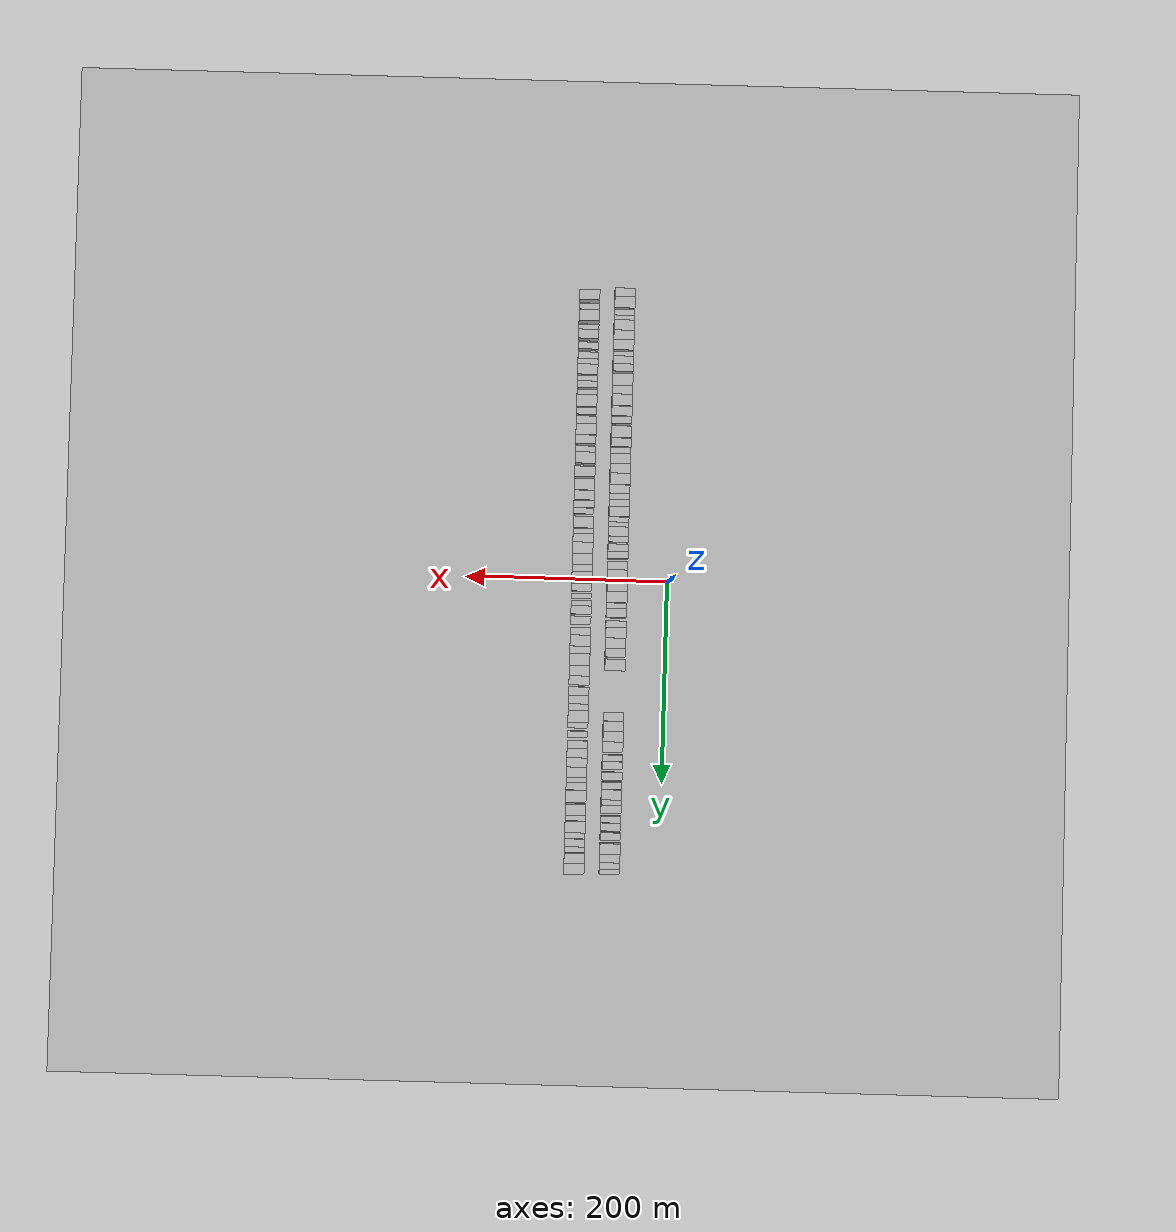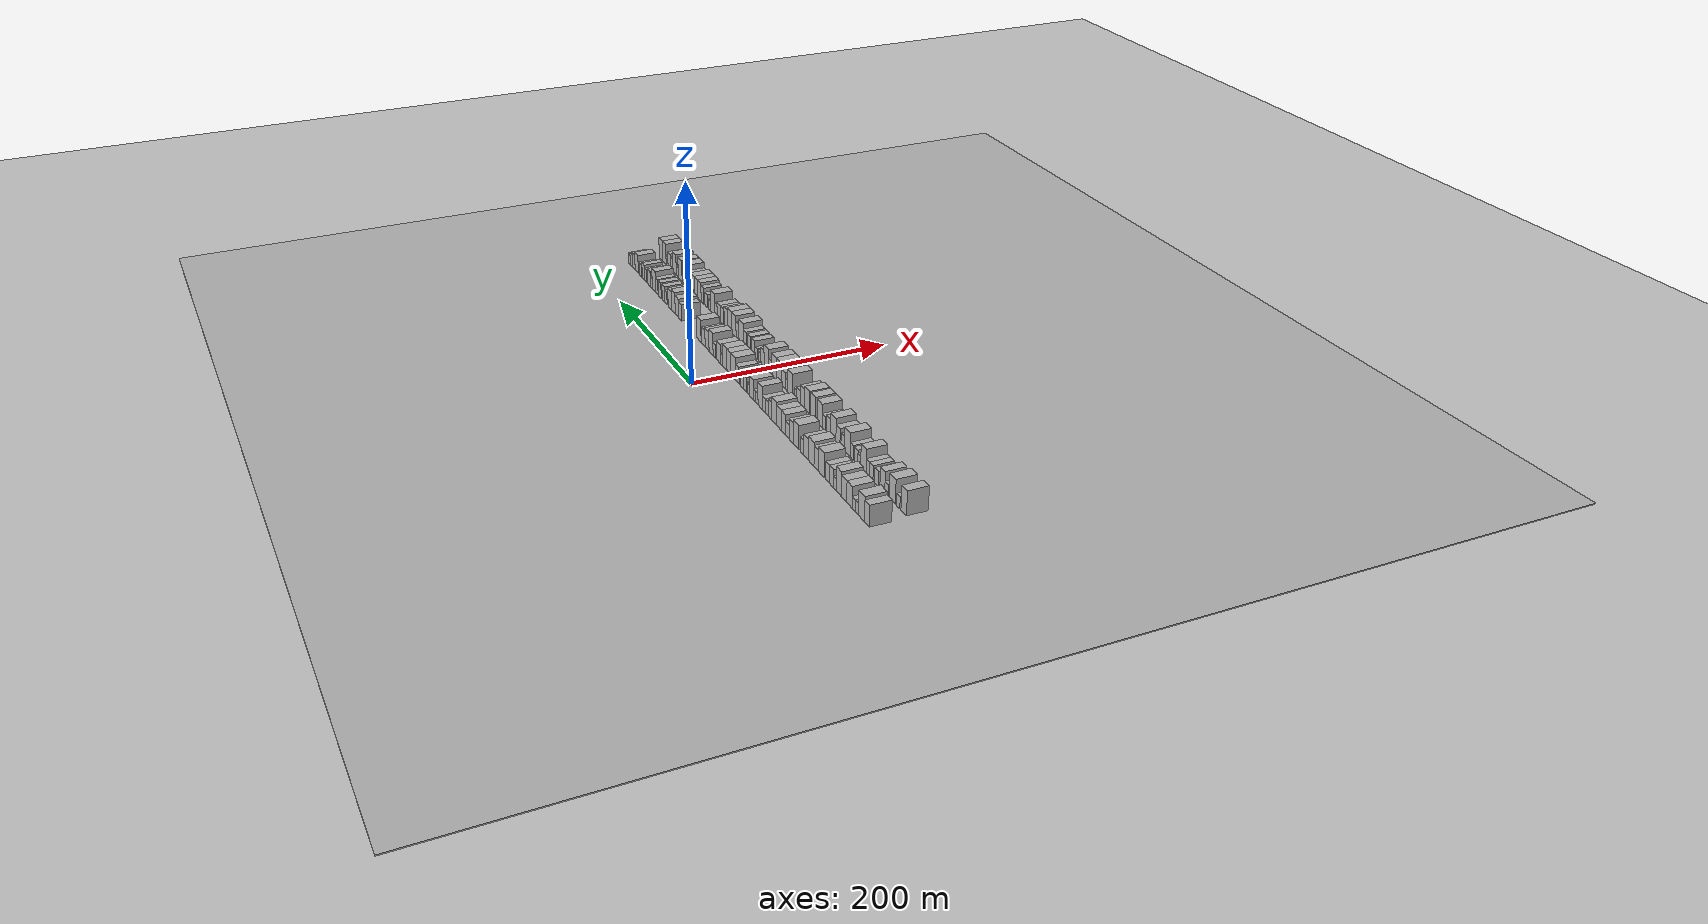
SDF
<?xml version="1.0" encoding="utf-8"?>

<sdf version="1.6">

   <world name="default">

      <gui fullscreen="0">

         <camera name="user_camera">

            <pose>-15 0 4.57585 0 0 0</pose>

            <view_controller>orbit</view_controller>

         </camera>

      </gui>

      <scene>

         <sky>

           <clouds>

             <speed>12</speed>

           </clouds>

         </sky>

         <ambient>0.4 0.4 0.4 1</ambient>

         <background>0.7 0.7 0.7 1</background>

         <shadows>1</shadows>

      </scene>

      <gravity>0 0 -9.8066</gravity>

      <magnetic_field>6e-06 2.3e-05 -4.2e-05</magnetic_field>

      <physics default="0" name="default_physics" type="ode">

         <ode>

            <solver>

               <type>quick</type>

               <iters>10</iters>

               <sor>1.0</sor>

               <use_dynamic_moi_rescaling>0</use_dynamic_moi_rescaling>

            </solver>

            <constraints>

               <cfm>0</cfm>

               <erp>0.2</erp>

               <contact_max_correcting_vel>100</contact_max_correcting_vel>

               <contact_surface_layer>0.001</contact_surface_layer>

            </constraints>

         </ode>

         <max_step_size>0.004</max_step_size>

         <real_time_factor>1</real_time_factor>

         <real_time_update_rate>250</real_time_update_rate>

      </physics>

      <light name="sun" type="directional">

         <cast_shadows>1</cast_shadows>

         <pose>0 0 10 0 0 0</pose>

         <diffuse>0.8 0.8 0.8 1</diffuse>

         <specular>0.2 0.2 0.2 1</specular>

         <attenuation>

            <range>1000</range>

            <constant>0.9</constant>

            <linear>0.01</linear>

            <quadratic>0.001</quadratic>

         </attenuation>

         <direction>-0.5 0.1 -0.9</direction>

      </light>

      <include>

         <name>ground_plane_1</name>

         <uri>model://HANNAS_ground_plane</uri>

         <pose>0 0 0  0 0 0</pose>

      </include>

      <include>

         <name>ground_plane_2</name>

         <uri>model://HANNAS_ground_plane</uri>

         <pose>100 0 0  0 0 0</pose>

      </include>

      <model name="building_1">

         <static>1</static>

         <pose frame="">50.0000 -285.5545 0 0.000000 0.000000 0.000000</pose>

         <link name="link">

            <pose frame="">0 0 10.50 0 0 0</pose>

            <collision name="collision">

               <geometry>

                  <box>

                     <size>20.0000 8.8911 21.0000</size>

                  </box>

               </geometry>

               <max_contacts>10</max_contacts>

               <surface>

                  <contact>

                     <ode/>

                  </contact>

                  <bounce/>

                  <friction>

                     <torsional>

                        <ode/>

                     </torsional>

                     <ode/>

                  </friction>

               </surface>

            </collision>

            <visual name="visual">

               <cast_shadows>0</cast_shadows>

               <geometry>

                  <box>

                     <size>20.0000 8.8911 21.0000</size>

                  </box>

               </geometry>

               <material>

                  <script>

                     <uri>model://HANNAS_wall/materials/scripts</uri>

                     <uri>model://HANNAS_wall/materials/textures</uri>

                     <name>vrc/HANNAS_wall</name>

                  </script>

               </material>

            </visual>

            <self_collide>0</self_collide>

            <enable_wind>0</enable_wind>

            <kinematic>0</kinematic>

         </link>

      </model>

      <model name="building_2">

         <static>1</static>

         <pose frame="">50.0000 -275.4508 0 0.000000 0.000000 0.000000</pose>

         <link name="link">

            <pose frame="">0 0 12.00 0 0 0</pose>

            <collision name="collision">

               <geometry>

                  <box>

                     <size>20.0000 11.3163 24.0000</size>

                  </box>

               </geometry>

               <max_contacts>10</max_contacts>

               <surface>

                  <contact>

                     <ode/>

                  </contact>

                  <bounce/>

                  <friction>

                     <torsional>

                        <ode/>

                     </torsional>

                     <ode/>

                  </friction>

               </surface>

            </collision>

            <visual name="visual">

               <cast_shadows>0</cast_shadows>

               <geometry>

                  <box>

                     <size>20.0000 11.3163 24.0000</size>

                  </box>

               </geometry>

               <material>

                  <script>

                     <uri>model://HANNAS_wall/materials/scripts</uri>

                     <uri>model://HANNAS_wall/materials/textures</uri>

                     <name>vrc/HANNAS_wall</name>

                  </script>

               </material>

            </visual>

            <self_collide>0</self_collide>

            <enable_wind>0</enable_wind>

            <kinematic>0</kinematic>

         </link>

      </model>

      <model name="building_3">

         <static>1</static>

         <pose frame="">50.0000 -267.0089 0 0.000000 0.000000 0.000000</pose>

         <link name="link">

            <pose frame="">0 0 6.00 0 0 0</pose>

            <collision name="collision">

               <geometry>

                  <box>

                     <size>20.0000 5.5675 12.0000</size>

                  </box>

               </geometry>

               <max_contacts>10</max_contacts>

               <surface>

                  <contact>

                     <ode/>

                  </contact>

                  <bounce/>

                  <friction>

                     <torsional>

                        <ode/>

                     </torsional>

                     <ode/>

                  </friction>

               </surface>

            </collision>

            <visual name="visual">

               <cast_shadows>0</cast_shadows>

               <geometry>

                  <box>

                     <size>20.0000 5.5675 12.0000</size>

                  </box>

               </geometry>

               <material>

                  <script>

                     <uri>model://HANNAS_wall/materials/scripts</uri>

                     <uri>model://HANNAS_wall/materials/textures</uri>

                     <name>vrc/HANNAS_wall</name>

                  </script>

               </material>

            </visual>

            <self_collide>0</self_collide>

            <enable_wind>0</enable_wind>

            <kinematic>0</kinematic>

         </link>

      </model>

      <model name="building_4">

         <static>1</static>

         <pose frame="">50.0000 -261.2701 0 0.000000 0.000000 0.000000</pose>

         <link name="link">

            <pose frame="">0 0 6.00 0 0 0</pose>

            <collision name="collision">

               <geometry>

                  <box>

                     <size>20.0000 5.9101 12.0000</size>

                  </box>

               </geometry>

               <max_contacts>10</max_contacts>

               <surface>

                  <contact>

                     <ode/>

                  </contact>

                  <bounce/>

                  <friction>

                     <torsional>

                        <ode/>

                     </torsional>

                     <ode/>

                  </friction>

               </surface>

            </collision>

            <visual name="visual">

               <cast_shadows>0</cast_shadows>

               <geometry>

                  <box>

                     <size>20.0000 5.9101 12.0000</size>

                  </box>

               </geometry>

               <material>

                  <script>

                     <uri>model://HANNAS_wall/materials/scripts</uri>

                     <uri>model://HANNAS_wall/materials/textures</uri>

                     <name>vrc/HANNAS_wall</name>

                  </script>

               </material>

            </visual>

            <self_collide>0</self_collide>

            <enable_wind>0</enable_wind>

            <kinematic>0</kinematic>

         </link>

      </model>

      <model name="building_5">

         <static>1</static>

         <pose frame="">50.0000 -253.2307 0 0.000000 0.000000 0.000000</pose>

         <link name="link">

            <pose frame="">0 0 10.50 0 0 0</pose>

            <collision name="collision">

               <geometry>

                  <box>

                     <size>20.0000 10.1686 21.0000</size>

                  </box>

               </geometry>

               <max_contacts>10</max_contacts>

               <surface>

                  <contact>

                     <ode/>

                  </contact>

                  <bounce/>

                  <friction>

                     <torsional>

                        <ode/>

                     </torsional>

                     <ode/>

                  </friction>

               </surface>

            </collision>

            <visual name="visual">

               <cast_shadows>0</cast_shadows>

               <geometry>

                  <box>

                     <size>20.0000 10.1686 21.0000</size>

                  </box>

               </geometry>

               <material>

                  <script>

                     <uri>model://HANNAS_wall/materials/scripts</uri>

                     <uri>model://HANNAS_wall/materials/textures</uri>

                     <name>vrc/HANNAS_wall</name>

                  </script>

               </material>

            </visual>

            <self_collide>0</self_collide>

            <enable_wind>0</enable_wind>

            <kinematic>0</kinematic>

         </link>

      </model>

      <model name="building_6">

         <static>1</static>

         <pose frame="">50.0000 -243.1957 0 0.000000 0.000000 0.000000</pose>

         <link name="link">

            <pose frame="">0 0 10.50 0 0 0</pose>

            <collision name="collision">

               <geometry>

                  <box>

                     <size>20.0000 9.9014 21.0000</size>

                  </box>

               </geometry>

               <max_contacts>10</max_contacts>

               <surface>

                  <contact>

                     <ode/>

                  </contact>

                  <bounce/>

                  <friction>

                     <torsional>

                        <ode/>

                     </torsional>

                     <ode/>

                  </friction>

               </surface>

            </collision>

            <visual name="visual">

               <cast_shadows>0</cast_shadows>

               <geometry>

                  <box>

                     <size>20.0000 9.9014 21.0000</size>

                  </box>

               </geometry>

               <material>

                  <script>

                     <uri>model://HANNAS_wall/materials/scripts</uri>

                     <uri>model://HANNAS_wall/materials/textures</uri>

                     <name>vrc/HANNAS_wall</name>

                  </script>

               </material>

            </visual>

            <self_collide>0</self_collide>

            <enable_wind>0</enable_wind>

            <kinematic>0</kinematic>

         </link>

      </model>

      <model name="building_7">

         <static>1</static>

         <pose frame="">50.0000 -233.1583 0 0.000000 0.000000 0.000000</pose>

         <link name="link">

            <pose frame="">0 0 12.00 0 0 0</pose>

            <collision name="collision">

               <geometry>

                  <box>

                     <size>20.0000 10.1734 24.0000</size>

                  </box>

               </geometry>

               <max_contacts>10</max_contacts>

               <surface>

                  <contact>

                     <ode/>

                  </contact>

                  <bounce/>

                  <friction>

                     <torsional>

                        <ode/>

                     </torsional>

                     <ode/>

                  </friction>

               </surface>

            </collision>

            <visual name="visual">

               <cast_shadows>0</cast_shadows>

               <geometry>

                  <box>

                     <size>20.0000 10.1734 24.0000</size>

                  </box>

               </geometry>

               <material>

                  <script>

                     <uri>model://HANNAS_wall/materials/scripts</uri>

                     <uri>model://HANNAS_wall/materials/textures</uri>

                     <name>vrc/HANNAS_wall</name>

                  </script>

               </material>

            </visual>

            <self_collide>0</self_collide>

            <enable_wind>0</enable_wind>

            <kinematic>0</kinematic>

         </link>

      </model>

      <model name="building_8">

         <static>1</static>

         <pose frame="">50.0000 -225.4317 0 0.000000 0.000000 0.000000</pose>

         <link name="link">

            <pose frame="">0 0 6.00 0 0 0</pose>

            <collision name="collision">

               <geometry>

                  <box>

                     <size>20.0000 5.2798 12.0000</size>

                  </box>

               </geometry>

               <max_contacts>10</max_contacts>

               <surface>

                  <contact>

                     <ode/>

                  </contact>

                  <bounce/>

                  <friction>

                     <torsional>

                        <ode/>

                     </torsional>

                     <ode/>

                  </friction>

               </surface>

            </collision>

            <visual name="visual">

               <cast_shadows>0</cast_shadows>

               <geometry>

                  <box>

                     <size>20.0000 5.2798 12.0000</size>

                  </box>

               </geometry>

               <material>

                  <script>

                     <uri>model://HANNAS_wall/materials/scripts</uri>

                     <uri>model://HANNAS_wall/materials/textures</uri>

                     <name>vrc/HANNAS_wall</name>

                  </script>

               </material>

            </visual>

            <self_collide>0</self_collide>

            <enable_wind>0</enable_wind>

            <kinematic>0</kinematic>

         </link>

      </model>

      <model name="building_9">

         <static>1</static>

         <pose frame="">50.0000 -218.8903 0 0.000000 0.000000 0.000000</pose>

         <link name="link">

            <pose frame="">0 0 9.00 0 0 0</pose>

            <collision name="collision">

               <geometry>

                  <box>

                     <size>20.0000 7.8029 18.0000</size>

                  </box>

               </geometry>

               <max_contacts>10</max_contacts>

               <surface>

                  <contact>

                     <ode/>

                  </contact>

                  <bounce/>

                  <friction>

                     <torsional>

                        <ode/>

                     </torsional>

                     <ode/>

                  </friction>

               </surface>

            </collision>

            <visual name="visual">

               <cast_shadows>0</cast_shadows>

               <geometry>

                  <box>

                     <size>20.0000 7.8029 18.0000</size>

                  </box>

               </geometry>

               <material>

                  <script>

                     <uri>model://HANNAS_wall/materials/scripts</uri>

                     <uri>model://HANNAS_wall/materials/textures</uri>

                     <name>vrc/HANNAS_wall</name>

                  </script>

               </material>

            </visual>

            <self_collide>0</self_collide>

            <enable_wind>0</enable_wind>

            <kinematic>0</kinematic>

         </link>

      </model>

      <model name="building_10">

         <static>1</static>

         <pose frame="">50.0000 -211.3066 0 0.000000 0.000000 0.000000</pose>

         <link name="link">

            <pose frame="">0 0 9.00 0 0 0</pose>

            <collision name="collision">

               <geometry>

                  <box>

                     <size>20.0000 7.3646 18.0000</size>

                  </box>

               </geometry>

               <max_contacts>10</max_contacts>

               <surface>

                  <contact>

                     <ode/>

                  </contact>

                  <bounce/>

                  <friction>

                     <torsional>

                        <ode/>

                     </torsional>

                     <ode/>

                  </friction>

               </surface>

            </collision>

            <visual name="visual">

               <cast_shadows>0</cast_shadows>

               <geometry>

                  <box>

                     <size>20.0000 7.3646 18.0000</size>

                  </box>

               </geometry>

               <material>

                  <script>

                     <uri>model://HANNAS_wall/materials/scripts</uri>

                     <uri>model://HANNAS_wall/materials/textures</uri>

                     <name>vrc/HANNAS_wall</name>

                  </script>

               </material>

            </visual>

            <self_collide>0</self_collide>

            <enable_wind>0</enable_wind>

            <kinematic>0</kinematic>

         </link>

      </model>

      <model name="building_11">

         <static>1</static>

         <pose frame="">50.0000 -198.7508 0 0.000000 0.000000 0.000000</pose>

         <link name="link">

            <pose frame="">0 0 12.00 0 0 0</pose>

            <collision name="collision">

               <geometry>

                  <box>

                     <size>20.0000 11.7470 24.0000</size>

                  </box>

               </geometry>

               <max_contacts>10</max_contacts>

               <surface>

                  <contact>

                     <ode/>

                  </contact>

                  <bounce/>

                  <friction>

                     <torsional>

                        <ode/>

                     </torsional>

                     <ode/>

                  </friction>

               </surface>

            </collision>

            <visual name="visual">

               <cast_shadows>0</cast_shadows>

               <geometry>

                  <box>

                     <size>20.0000 11.7470 24.0000</size>

                  </box>

               </geometry>

               <material>

                  <script>

                     <uri>model://HANNAS_wall/materials/scripts</uri>

                     <uri>model://HANNAS_wall/materials/textures</uri>

                     <name>vrc/HANNAS_wall</name>

                  </script>

               </material>

            </visual>

            <self_collide>0</self_collide>

            <enable_wind>0</enable_wind>

            <kinematic>0</kinematic>

         </link>

      </model>

      <model name="building_12">

         <static>1</static>

         <pose frame="">50.0000 -188.5699 0 0.000000 0.000000 0.000000</pose>

         <link name="link">

            <pose frame="">0 0 10.50 0 0 0</pose>

            <collision name="collision">

               <geometry>

                  <box>

                     <size>20.0000 8.6148 21.0000</size>

                  </box>

               </geometry>

               <max_contacts>10</max_contacts>

               <surface>

                  <contact>

                     <ode/>

                  </contact>

                  <bounce/>

                  <friction>

                     <torsional>

                        <ode/>

                     </torsional>

                     <ode/>

                  </friction>

               </surface>

            </collision>

            <visual name="visual">

               <cast_shadows>0</cast_shadows>

               <geometry>

                  <box>

                     <size>20.0000 8.6148 21.0000</size>

                  </box>

               </geometry>

               <material>

                  <script>

                     <uri>model://HANNAS_wall/materials/scripts</uri>

                     <uri>model://HANNAS_wall/materials/textures</uri>

                     <name>vrc/HANNAS_wall</name>

                  </script>

               </material>

            </visual>

            <self_collide>0</self_collide>

            <enable_wind>0</enable_wind>

            <kinematic>0</kinematic>

         </link>

      </model>

      <model name="building_13">

         <static>1</static>

         <pose frame="">50.0000 -178.4441 0 0.000000 0.000000 0.000000</pose>

         <link name="link">

            <pose frame="">0 0 12.00 0 0 0</pose>

            <collision name="collision">

               <geometry>

                  <box>

                     <size>20.0000 11.6368 24.0000</size>

                  </box>

               </geometry>

               <max_contacts>10</max_contacts>

               <surface>

                  <contact>

                     <ode/>

                  </contact>

                  <bounce/>

                  <friction>

                     <torsional>

                        <ode/>

                     </torsional>

                     <ode/>

                  </friction>

               </surface>

            </collision>

            <visual name="visual">

               <cast_shadows>0</cast_shadows>

               <geometry>

                  <box>

                     <size>20.0000 11.6368 24.0000</size>

                  </box>

               </geometry>

               <material>

                  <script>

                     <uri>model://HANNAS_wall/materials/scripts</uri>

                     <uri>model://HANNAS_wall/materials/textures</uri>

                     <name>vrc/HANNAS_wall</name>

                  </script>

               </material>

            </visual>

            <self_collide>0</self_collide>

            <enable_wind>0</enable_wind>

            <kinematic>0</kinematic>

         </link>

      </model>

      <model name="building_14">

         <static>1</static>

         <pose frame="">50.0000 -167.7657 0 0.000000 0.000000 0.000000</pose>

         <link name="link">

            <pose frame="">0 0 10.50 0 0 0</pose>

            <collision name="collision">

               <geometry>

                  <box>

                     <size>20.0000 9.7201 21.0000</size>

                  </box>

               </geometry>

               <max_contacts>10</max_contacts>

               <surface>

                  <contact>

                     <ode/>

                  </contact>

                  <bounce/>

                  <friction>

                     <torsional>

                        <ode/>

                     </torsional>

                     <ode/>

                  </friction>

               </surface>

            </collision>

            <visual name="visual">

               <cast_shadows>0</cast_shadows>

               <geometry>

                  <box>

                     <size>20.0000 9.7201 21.0000</size>

                  </box>

               </geometry>

               <material>

                  <script>

                     <uri>model://HANNAS_wall/materials/scripts</uri>

                     <uri>model://HANNAS_wall/materials/textures</uri>

                     <name>vrc/HANNAS_wall</name>

                  </script>

               </material>

            </visual>

            <self_collide>0</self_collide>

            <enable_wind>0</enable_wind>

            <kinematic>0</kinematic>

         </link>

      </model>

      <model name="building_15">

         <static>1</static>

         <pose frame="">50.0000 -159.3174 0 0.000000 0.000000 0.000000</pose>

         <link name="link">

            <pose frame="">0 0 7.50 0 0 0</pose>

            <collision name="collision">

               <geometry>

                  <box>

                     <size>20.0000 7.1764 15.0000</size>

                  </box>

               </geometry>

               <max_contacts>10</max_contacts>

               <surface>

                  <contact>

                     <ode/>

                  </contact>

                  <bounce/>

                  <friction>

                     <torsional>

                        <ode/>

                     </torsional>

                     <ode/>

                  </friction>

               </surface>

            </collision>

            <visual name="visual">

               <cast_shadows>0</cast_shadows>

               <geometry>

                  <box>

                     <size>20.0000 7.1764 15.0000</size>

                  </box>

               </geometry>

               <material>

                  <script>

                     <uri>model://HANNAS_wall/materials/scripts</uri>

                     <uri>model://HANNAS_wall/materials/textures</uri>

                     <name>vrc/HANNAS_wall</name>

                  </script>

               </material>

            </visual>

            <self_collide>0</self_collide>

            <enable_wind>0</enable_wind>

            <kinematic>0</kinematic>

         </link>

      </model>

      <model name="building_16">

         <static>1</static>

         <pose frame="">50.0000 -146.8509 0 0.000000 0.000000 0.000000</pose>

         <link name="link">

            <pose frame="">0 0 12.00 0 0 0</pose>

            <collision name="collision">

               <geometry>

                  <box>

                     <size>20.0000 11.7566 24.0000</size>

                  </box>

               </geometry>

               <max_contacts>10</max_contacts>

               <surface>

                  <contact>

                     <ode/>

                  </contact>

                  <bounce/>

                  <friction>

                     <torsional>

                        <ode/>

                     </torsional>

                     <ode/>

                  </friction>

               </surface>

            </collision>

            <visual name="visual">

               <cast_shadows>0</cast_shadows>

               <geometry>

                  <box>

                     <size>20.0000 11.7566 24.0000</size>

                  </box>

               </geometry>

               <material>

                  <script>

                     <uri>model://HANNAS_wall/materials/scripts</uri>

                     <uri>model://HANNAS_wall/materials/textures</uri>

                     <name>vrc/HANNAS_wall</name>

                  </script>

               </material>

            </visual>

            <self_collide>0</self_collide>

            <enable_wind>0</enable_wind>

            <kinematic>0</kinematic>

         </link>

      </model>

      <model name="building_17">

         <static>1</static>

         <pose frame="">50.0000 -136.6007 0 0.000000 0.000000 0.000000</pose>

         <link name="link">

            <pose frame="">0 0 10.50 0 0 0</pose>

            <collision name="collision">

               <geometry>

                  <box>

                     <size>20.0000 8.7438 21.0000</size>

                  </box>

               </geometry>

               <max_contacts>10</max_contacts>

               <surface>

                  <contact>

                     <ode/>

                  </contact>

                  <bounce/>

                  <friction>

                     <torsional>

                        <ode/>

                     </torsional>

                     <ode/>

                  </friction>

               </surface>

            </collision>

            <visual name="visual">

               <cast_shadows>0</cast_shadows>

               <geometry>

                  <box>

                     <size>20.0000 8.7438 21.0000</size>

                  </box>

               </geometry>

               <material>

                  <script>

                     <uri>model://HANNAS_wall/materials/scripts</uri>

                     <uri>model://HANNAS_wall/materials/textures</uri>

                     <name>vrc/HANNAS_wall</name>

                  </script>

               </material>

            </visual>

            <self_collide>0</self_collide>

            <enable_wind>0</enable_wind>

            <kinematic>0</kinematic>

         </link>

      </model>

      <model name="building_18">

         <static>1</static>

         <pose frame="">50.0000 -128.8635 0 0.000000 0.000000 0.000000</pose>

         <link name="link">

            <pose frame="">0 0 7.50 0 0 0</pose>

            <collision name="collision">

               <geometry>

                  <box>

                     <size>20.0000 6.7308 15.0000</size>

                  </box>

               </geometry>

               <max_contacts>10</max_contacts>

               <surface>

                  <contact>

                     <ode/>

                  </contact>

                  <bounce/>

                  <friction>

                     <torsional>

                        <ode/>

                     </torsional>

                     <ode/>

                  </friction>

               </surface>

            </collision>

            <visual name="visual">

               <cast_shadows>0</cast_shadows>

               <geometry>

                  <box>

                     <size>20.0000 6.7308 15.0000</size>

                  </box>

               </geometry>

               <material>

                  <script>

                     <uri>model://HANNAS_wall/materials/scripts</uri>

                     <uri>model://HANNAS_wall/materials/textures</uri>

                     <name>vrc/HANNAS_wall</name>

                  </script>

               </material>

            </visual>

            <self_collide>0</self_collide>

            <enable_wind>0</enable_wind>

            <kinematic>0</kinematic>

         </link>

      </model>

      <model name="building_19">

         <static>1</static>

         <pose frame="">50.0000 -120.5768 0 0.000000 0.000000 0.000000</pose>

         <link name="link">

            <pose frame="">0 0 10.50 0 0 0</pose>

            <collision name="collision">

               <geometry>

                  <box>

                     <size>20.0000 9.8427 21.0000</size>

                  </box>

               </geometry>

               <max_contacts>10</max_contacts>

               <surface>

                  <contact>

                     <ode/>

                  </contact>

                  <bounce/>

                  <friction>

                     <torsional>

                        <ode/>

                     </torsional>

                     <ode/>

                  </friction>

               </surface>

            </collision>

            <visual name="visual">

               <cast_shadows>0</cast_shadows>

               <geometry>

                  <box>

                     <size>20.0000 9.8427 21.0000</size>

                  </box>

               </geometry>

               <material>

                  <script>

                     <uri>model://HANNAS_wall/materials/scripts</uri>

                     <uri>model://HANNAS_wall/materials/textures</uri>

                     <name>vrc/HANNAS_wall</name>

                  </script>

               </material>

            </visual>

            <self_collide>0</self_collide>

            <enable_wind>0</enable_wind>

            <kinematic>0</kinematic>

         </link>

      </model>

      <model name="building_20">

         <static>1</static>

         <pose frame="">50.0000 -110.8102 0 0.000000 0.000000 0.000000</pose>

         <link name="link">

            <pose frame="">0 0 10.50 0 0 0</pose>

            <collision name="collision">

               <geometry>

                  <box>

                     <size>20.0000 9.6905 21.0000</size>

                  </box>

               </geometry>

               <max_contacts>10</max_contacts>

               <surface>

                  <contact>

                     <ode/>

                  </contact>

                  <bounce/>

                  <friction>

                     <torsional>

                        <ode/>

                     </torsional>

                     <ode/>

                  </friction>

               </surface>

            </collision>

            <visual name="visual">

               <cast_shadows>0</cast_shadows>

               <geometry>

                  <box>

                     <size>20.0000 9.6905 21.0000</size>

                  </box>

               </geometry>

               <material>

                  <script>

                     <uri>model://HANNAS_wall/materials/scripts</uri>

                     <uri>model://HANNAS_wall/materials/textures</uri>

                     <name>vrc/HANNAS_wall</name>

                  </script>

               </material>

            </visual>

            <self_collide>0</self_collide>

            <enable_wind>0</enable_wind>

            <kinematic>0</kinematic>

         </link>

      </model>

      <model name="building_21">

         <static>1</static>

         <pose frame="">50.0000 -100.3670 0 0.000000 0.000000 0.000000</pose>

         <link name="link">

            <pose frame="">0 0 12.00 0 0 0</pose>

            <collision name="collision">

               <geometry>

                  <box>

                     <size>20.0000 11.1959 24.0000</size>

                  </box>

               </geometry>

               <max_contacts>10</max_contacts>

               <surface>

                  <contact>

                     <ode/>

                  </contact>

                  <bounce/>

                  <friction>

                     <torsional>

                        <ode/>

                     </torsional>

                     <ode/>

                  </friction>

               </surface>

            </collision>

            <visual name="visual">

               <cast_shadows>0</cast_shadows>

               <geometry>

                  <box>

                     <size>20.0000 11.1959 24.0000</size>

                  </box>

               </geometry>

               <material>

                  <script>

                     <uri>model://HANNAS_wall/materials/scripts</uri>

                     <uri>model://HANNAS_wall/materials/textures</uri>

                     <name>vrc/HANNAS_wall</name>

                  </script>

               </material>

            </visual>

            <self_collide>0</self_collide>

            <enable_wind>0</enable_wind>

            <kinematic>0</kinematic>

         </link>

      </model>

      <model name="building_22">

         <static>1</static>

         <pose frame="">50.0000 -90.5872 0 0.000000 0.000000 0.000000</pose>

         <link name="link">

            <pose frame="">0 0 9.00 0 0 0</pose>

            <collision name="collision">

               <geometry>

                  <box>

                     <size>20.0000 8.3636 18.0000</size>

                  </box>

               </geometry>

               <max_contacts>10</max_contacts>

               <surface>

                  <contact>

                     <ode/>

                  </contact>

                  <bounce/>

                  <friction>

                     <torsional>

                        <ode/>

                     </torsional>

                     <ode/>

                  </friction>

               </surface>

            </collision>

            <visual name="visual">

               <cast_shadows>0</cast_shadows>

               <geometry>

                  <box>

                     <size>20.0000 8.3636 18.0000</size>

                  </box>

               </geometry>

               <material>

                  <script>

                     <uri>model://HANNAS_wall/materials/scripts</uri>

                     <uri>model://HANNAS_wall/materials/textures</uri>

                     <name>vrc/HANNAS_wall</name>

                  </script>

               </material>

            </visual>

            <self_collide>0</self_collide>

            <enable_wind>0</enable_wind>

            <kinematic>0</kinematic>

         </link>

      </model>

      <model name="building_23">

         <static>1</static>

         <pose frame="">50.0000 -83.3970 0 0.000000 0.000000 0.000000</pose>

         <link name="link">

            <pose frame="">0 0 7.50 0 0 0</pose>

            <collision name="collision">

               <geometry>

                  <box>

                     <size>20.0000 6.0168 15.0000</size>

                  </box>

               </geometry>

               <max_contacts>10</max_contacts>

               <surface>

                  <contact>

                     <ode/>

                  </contact>

                  <bounce/>

                  <friction>

                     <torsional>

                        <ode/>

                     </torsional>

                     <ode/>

                  </friction>

               </surface>

            </collision>

            <visual name="visual">

               <cast_shadows>0</cast_shadows>

               <geometry>

                  <box>

                     <size>20.0000 6.0168 15.0000</size>

                  </box>

               </geometry>

               <material>

                  <script>

                     <uri>model://HANNAS_wall/materials/scripts</uri>

                     <uri>model://HANNAS_wall/materials/textures</uri>

                     <name>vrc/HANNAS_wall</name>

                  </script>

               </material>

            </visual>

            <self_collide>0</self_collide>

            <enable_wind>0</enable_wind>

            <kinematic>0</kinematic>

         </link>

      </model>

      <model name="building_24">

         <static>1</static>

         <pose frame="">50.0000 -76.6673 0 0.000000 0.000000 0.000000</pose>

         <link name="link">

            <pose frame="">0 0 7.50 0 0 0</pose>

            <collision name="collision">

               <geometry>

                  <box>

                     <size>20.0000 7.4427 15.0000</size>

                  </box>

               </geometry>

               <max_contacts>10</max_contacts>

               <surface>

                  <contact>

                     <ode/>

                  </contact>

                  <bounce/>

                  <friction>

                     <torsional>

                        <ode/>

                     </torsional>

                     <ode/>

                  </friction>

               </surface>

            </collision>

            <visual name="visual">

               <cast_shadows>0</cast_shadows>

               <geometry>

                  <box>

                     <size>20.0000 7.4427 15.0000</size>

                  </box>

               </geometry>

               <material>

                  <script>

                     <uri>model://HANNAS_wall/materials/scripts</uri>

                     <uri>model://HANNAS_wall/materials/textures</uri>

                     <name>vrc/HANNAS_wall</name>

                  </script>

               </material>

            </visual>

            <self_collide>0</self_collide>

            <enable_wind>0</enable_wind>

            <kinematic>0</kinematic>

         </link>

      </model>

      <model name="building_25">

         <static>1</static>

         <pose frame="">50.0000 -68.0999 0 0.000000 0.000000 0.000000</pose>

         <link name="link">

            <pose frame="">0 0 12.00 0 0 0</pose>

            <collision name="collision">

               <geometry>

                  <box>

                     <size>20.0000 9.6921 24.0000</size>

                  </box>

               </geometry>

               <max_contacts>10</max_contacts>

               <surface>

                  <contact>

                     <ode/>

                  </contact>

                  <bounce/>

                  <friction>

                     <torsional>

                        <ode/>

                     </torsional>

                     <ode/>

                  </friction>

               </surface>

            </collision>

            <visual name="visual">

               <cast_shadows>0</cast_shadows>

               <geometry>

                  <box>

                     <size>20.0000 9.6921 24.0000</size>

                  </box>

               </geometry>

               <material>

                  <script>

                     <uri>model://HANNAS_wall/materials/scripts</uri>

                     <uri>model://HANNAS_wall/materials/textures</uri>

                     <name>vrc/HANNAS_wall</name>

                  </script>

               </material>

            </visual>

            <self_collide>0</self_collide>

            <enable_wind>0</enable_wind>

            <kinematic>0</kinematic>

         </link>

      </model>

      <model name="building_26">

         <static>1</static>

         <pose frame="">50.0000 -60.7385 0 0.000000 0.000000 0.000000</pose>

         <link name="link">

            <pose frame="">0 0 6.00 0 0 0</pose>

            <collision name="collision">

               <geometry>

                  <box>

                     <size>20.0000 5.0307 12.0000</size>

                  </box>

               </geometry>

               <max_contacts>10</max_contacts>

               <surface>

                  <contact>

                     <ode/>

                  </contact>

                  <bounce/>

                  <friction>

                     <torsional>

                        <ode/>

                     </torsional>

                     <ode/>

                  </friction>

               </surface>

            </collision>

            <visual name="visual">

               <cast_shadows>0</cast_shadows>

               <geometry>

                  <box>

                     <size>20.0000 5.0307 12.0000</size>

                  </box>

               </geometry>

               <material>

                  <script>

                     <uri>model://HANNAS_wall/materials/scripts</uri>

                     <uri>model://HANNAS_wall/materials/textures</uri>

                     <name>vrc/HANNAS_wall</name>

                  </script>

               </material>

            </visual>

            <self_collide>0</self_collide>

            <enable_wind>0</enable_wind>

            <kinematic>0</kinematic>

         </link>

      </model>

      <model name="building_27">

         <static>1</static>

         <pose frame="">50.0000 -55.6057 0 0.000000 0.000000 0.000000</pose>

         <link name="link">

            <pose frame="">0 0 6.00 0 0 0</pose>

            <collision name="collision">

               <geometry>

                  <box>

                     <size>20.0000 5.2350 12.0000</size>

                  </box>

               </geometry>

               <max_contacts>10</max_contacts>

               <surface>

                  <contact>

                     <ode/>

                  </contact>

                  <bounce/>

                  <friction>

                     <torsional>

                        <ode/>

                     </torsional>

                     <ode/>

                  </friction>

               </surface>

            </collision>

            <visual name="visual">

               <cast_shadows>0</cast_shadows>

               <geometry>

                  <box>

                     <size>20.0000 5.2350 12.0000</size>

                  </box>

               </geometry>

               <material>

                  <script>

                     <uri>model://HANNAS_wall/materials/scripts</uri>

                     <uri>model://HANNAS_wall/materials/textures</uri>

                     <name>vrc/HANNAS_wall</name>

                  </script>

               </material>

            </visual>

            <self_collide>0</self_collide>

            <enable_wind>0</enable_wind>

            <kinematic>0</kinematic>

         </link>

      </model>

      <model name="building_28">

         <static>1</static>

         <pose frame="">50.0000 -48.3343 0 0.000000 0.000000 0.000000</pose>

         <link name="link">

            <pose frame="">0 0 10.50 0 0 0</pose>

            <collision name="collision">

               <geometry>

                  <box>

                     <size>20.0000 9.3079 21.0000</size>

                  </box>

               </geometry>

               <max_contacts>10</max_contacts>

               <surface>

                  <contact>

                     <ode/>

                  </contact>

                  <bounce/>

                  <friction>

                     <torsional>

                        <ode/>

                     </torsional>

                     <ode/>

                  </friction>

               </surface>

            </collision>

            <visual name="visual">

               <cast_shadows>0</cast_shadows>

               <geometry>

                  <box>

                     <size>20.0000 9.3079 21.0000</size>

                  </box>

               </geometry>

               <material>

                  <script>

                     <uri>model://HANNAS_wall/materials/scripts</uri>

                     <uri>model://HANNAS_wall/materials/textures</uri>

                     <name>vrc/HANNAS_wall</name>

                  </script>

               </material>

            </visual>

            <self_collide>0</self_collide>

            <enable_wind>0</enable_wind>

            <kinematic>0</kinematic>

         </link>

      </model>

      <model name="building_29">

         <static>1</static>

         <pose frame="">50.0000 -40.9712 0 0.000000 0.000000 0.000000</pose>

         <link name="link">

            <pose frame="">0 0 6.00 0 0 0</pose>

            <collision name="collision">

               <geometry>

                  <box>

                     <size>20.0000 5.4182 12.0000</size>

                  </box>

               </geometry>

               <max_contacts>10</max_contacts>

               <surface>

                  <contact>

                     <ode/>

                  </contact>

                  <bounce/>

                  <friction>

                     <torsional>

                        <ode/>

                     </torsional>

                     <ode/>

                  </friction>

               </surface>

            </collision>

            <visual name="visual">

               <cast_shadows>0</cast_shadows>

               <geometry>

                  <box>

                     <size>20.0000 5.4182 12.0000</size>

                  </box>

               </geometry>

               <material>

                  <script>

                     <uri>model://HANNAS_wall/materials/scripts</uri>

                     <uri>model://HANNAS_wall/materials/textures</uri>

                     <name>vrc/HANNAS_wall</name>

                  </script>

               </material>

            </visual>

            <self_collide>0</self_collide>

            <enable_wind>0</enable_wind>

            <kinematic>0</kinematic>

         </link>

      </model>

      <model name="building_30">

         <static>1</static>

         <pose frame="">50.0000 -32.5874 0 0.000000 0.000000 0.000000</pose>

         <link name="link">

            <pose frame="">0 0 7.50 0 0 0</pose>

            <collision name="collision">

               <geometry>

                  <box>

                     <size>20.0000 7.3494 15.0000</size>

                  </box>

               </geometry>

               <max_contacts>10</max_contacts>

               <surface>

                  <contact>

                     <ode/>

                  </contact>

                  <bounce/>

                  <friction>

                     <torsional>

                        <ode/>

                     </torsional>

                     <ode/>

                  </friction>

               </surface>

            </collision>

            <visual name="visual">

               <cast_shadows>0</cast_shadows>

               <geometry>

                  <box>

                     <size>20.0000 7.3494 15.0000</size>

                  </box>

               </geometry>

               <material>

                  <script>

                     <uri>model://HANNAS_wall/materials/scripts</uri>

                     <uri>model://HANNAS_wall/materials/textures</uri>

                     <name>vrc/HANNAS_wall</name>

                  </script>

               </material>

            </visual>

            <self_collide>0</self_collide>

            <enable_wind>0</enable_wind>

            <kinematic>0</kinematic>

         </link>

      </model>

      <model name="building_31">

         <static>1</static>

         <pose frame="">50.0000 -25.2734 0 0.000000 0.000000 0.000000</pose>

         <link name="link">

            <pose frame="">0 0 9.00 0 0 0</pose>

            <collision name="collision">

               <geometry>

                  <box>

                     <size>20.0000 7.2786 18.0000</size>

                  </box>

               </geometry>

               <max_contacts>10</max_contacts>

               <surface>

                  <contact>

                     <ode/>

                  </contact>

                  <bounce/>

                  <friction>

                     <torsional>

                        <ode/>

                     </torsional>

                     <ode/>

                  </friction>

               </surface>

            </collision>

            <visual name="visual">

               <cast_shadows>0</cast_shadows>

               <geometry>

                  <box>

                     <size>20.0000 7.2786 18.0000</size>

                  </box>

               </geometry>

               <material>

                  <script>

                     <uri>model://HANNAS_wall/materials/scripts</uri>

                     <uri>model://HANNAS_wall/materials/textures</uri>

                     <name>vrc/HANNAS_wall</name>

                  </script>

               </material>

            </visual>

            <self_collide>0</self_collide>

            <enable_wind>0</enable_wind>

            <kinematic>0</kinematic>

         </link>

      </model>

      <model name="building_32">

         <static>1</static>

         <pose frame="">50.0000 -14.4998 0 0.000000 0.000000 0.000000</pose>

         <link name="link">

            <pose frame="">0 0 9.00 0 0 0</pose>

            <collision name="collision">

               <geometry>

                  <box>

                     <size>20.0000 8.2685 18.0000</size>

                  </box>

               </geometry>

               <max_contacts>10</max_contacts>

               <surface>

                  <contact>

                     <ode/>

                  </contact>

                  <bounce/>

                  <friction>

                     <torsional>

                        <ode/>

                     </torsional>

                     <ode/>

                  </friction>

               </surface>

            </collision>

            <visual name="visual">

               <cast_shadows>0</cast_shadows>

               <geometry>

                  <box>

                     <size>20.0000 8.2685 18.0000</size>

                  </box>

               </geometry>

               <material>

                  <script>

                     <uri>model://HANNAS_wall/materials/scripts</uri>

                     <uri>model://HANNAS_wall/materials/textures</uri>

                     <name>vrc/HANNAS_wall</name>

                  </script>

               </material>

            </visual>

            <self_collide>0</self_collide>

            <enable_wind>0</enable_wind>

            <kinematic>0</kinematic>

         </link>

      </model>

      <model name="building_33">

         <static>1</static>

         <pose frame="">50.0000 -4.4543 0 0.000000 0.000000 0.000000</pose>

         <link name="link">

            <pose frame="">0 0 12.00 0 0 0</pose>

            <collision name="collision">

               <geometry>

                  <box>

                     <size>20.0000 11.8226 24.0000</size>

                  </box>

               </geometry>

               <max_contacts>10</max_contacts>

               <surface>

                  <contact>

                     <ode/>

                  </contact>

                  <bounce/>

                  <friction>

                     <torsional>

                        <ode/>

                     </torsional>

                     <ode/>

                  </friction>

               </surface>

            </collision>

            <visual name="visual">

               <cast_shadows>0</cast_shadows>

               <geometry>

                  <box>

                     <size>20.0000 11.8226 24.0000</size>

                  </box>

               </geometry>

               <material>

                  <script>

                     <uri>model://HANNAS_wall/materials/scripts</uri>

                     <uri>model://HANNAS_wall/materials/textures</uri>

                     <name>vrc/HANNAS_wall</name>

                  </script>

               </material>

            </visual>

            <self_collide>0</self_collide>

            <enable_wind>0</enable_wind>

            <kinematic>0</kinematic>

         </link>

      </model>

      <model name="building_34">

         <static>1</static>

         <pose frame="">50.0000 6.3101 0 0.000000 0.000000 0.000000</pose>

         <link name="link">

            <pose frame="">0 0 12.00 0 0 0</pose>

            <collision name="collision">

               <geometry>

                  <box>

                     <size>20.0000 9.7060 24.0000</size>

                  </box>

               </geometry>

               <max_contacts>10</max_contacts>

               <surface>

                  <contact>

                     <ode/>

                  </contact>

                  <bounce/>

                  <friction>

                     <torsional>

                        <ode/>

                     </torsional>

                     <ode/>

                  </friction>

               </surface>

            </collision>

            <visual name="visual">

               <cast_shadows>0</cast_shadows>

               <geometry>

                  <box>

                     <size>20.0000 9.7060 24.0000</size>

                  </box>

               </geometry>

               <material>

                  <script>

                     <uri>model://HANNAS_wall/materials/scripts</uri>

                     <uri>model://HANNAS_wall/materials/textures</uri>

                     <name>vrc/HANNAS_wall</name>

                  </script>

               </material>

            </visual>

            <self_collide>0</self_collide>

            <enable_wind>0</enable_wind>

            <kinematic>0</kinematic>

         </link>

      </model>

      <model name="building_35">

         <static>1</static>

         <pose frame="">50.0000 16.6346 0 0.000000 0.000000 0.000000</pose>

         <link name="link">

            <pose frame="">0 0 12.00 0 0 0</pose>

            <collision name="collision">

               <geometry>

                  <box>

                     <size>20.0000 10.9430 24.0000</size>

                  </box>

               </geometry>

               <max_contacts>10</max_contacts>

               <surface>

                  <contact>

                     <ode/>

                  </contact>

                  <bounce/>

                  <friction>

                     <torsional>

                        <ode/>

                     </torsional>

                     <ode/>

                  </friction>

               </surface>

            </collision>

            <visual name="visual">

               <cast_shadows>0</cast_shadows>

               <geometry>

                  <box>

                     <size>20.0000 10.9430 24.0000</size>

                  </box>

               </geometry>

               <material>

                  <script>

                     <uri>model://HANNAS_wall/materials/scripts</uri>

                     <uri>model://HANNAS_wall/materials/textures</uri>

                     <name>vrc/HANNAS_wall</name>

                  </script>

               </material>

            </visual>

            <self_collide>0</self_collide>

            <enable_wind>0</enable_wind>

            <kinematic>0</kinematic>

         </link>

      </model>

      <model name="building_36">

         <static>1</static>

         <pose frame="">50.0000 24.8381 0 0.000000 0.000000 0.000000</pose>

         <link name="link">

            <pose frame="">0 0 6.00 0 0 0</pose>

            <collision name="collision">

               <geometry>

                  <box>

                     <size>20.0000 5.4641 12.0000</size>

                  </box>

               </geometry>

               <max_contacts>10</max_contacts>

               <surface>

                  <contact>

                     <ode/>

                  </contact>

                  <bounce/>

                  <friction>

                     <torsional>

                        <ode/>

                     </torsional>

                     <ode/>

                  </friction>

               </surface>

            </collision>

            <visual name="visual">

               <cast_shadows>0</cast_shadows>

               <geometry>

                  <box>

                     <size>20.0000 5.4641 12.0000</size>

                  </box>

               </geometry>

               <material>

                  <script>

                     <uri>model://HANNAS_wall/materials/scripts</uri>

                     <uri>model://HANNAS_wall/materials/textures</uri>

                     <name>vrc/HANNAS_wall</name>

                  </script>

               </material>

            </visual>

            <self_collide>0</self_collide>

            <enable_wind>0</enable_wind>

            <kinematic>0</kinematic>

         </link>

      </model>

      <model name="building_37">

         <static>1</static>

         <pose frame="">50.0000 32.2049 0 0.000000 0.000000 0.000000</pose>

         <link name="link">

            <pose frame="">0 0 10.50 0 0 0</pose>

            <collision name="collision">

               <geometry>

                  <box>

                     <size>20.0000 9.2696 21.0000</size>

                  </box>

               </geometry>

               <max_contacts>10</max_contacts>

               <surface>

                  <contact>

                     <ode/>

                  </contact>

                  <bounce/>

                  <friction>

                     <torsional>

                        <ode/>

                     </torsional>

                     <ode/>

                  </friction>

               </surface>

            </collision>

            <visual name="visual">

               <cast_shadows>0</cast_shadows>

               <geometry>

                  <box>

                     <size>20.0000 9.2696 21.0000</size>

                  </box>

               </geometry>

               <material>

                  <script>

                     <uri>model://HANNAS_wall/materials/scripts</uri>

                     <uri>model://HANNAS_wall/materials/textures</uri>

                     <name>vrc/HANNAS_wall</name>

                  </script>

               </material>

            </visual>

            <self_collide>0</self_collide>

            <enable_wind>0</enable_wind>

            <kinematic>0</kinematic>

         </link>

      </model>

      <model name="building_38">

         <static>1</static>

         <pose frame="">50.0000 43.1029 0 0.000000 0.000000 0.000000</pose>

         <link name="link">

            <pose frame="">0 0 7.50 0 0 0</pose>

            <collision name="collision">

               <geometry>

                  <box>

                     <size>20.0000 6.5264 15.0000</size>

                  </box>

               </geometry>

               <max_contacts>10</max_contacts>

               <surface>

                  <contact>

                     <ode/>

                  </contact>

                  <bounce/>

                  <friction>

                     <torsional>

                        <ode/>

                     </torsional>

                     <ode/>

                  </friction>

               </surface>

            </collision>

            <visual name="visual">

               <cast_shadows>0</cast_shadows>

               <geometry>

                  <box>

                     <size>20.0000 6.5264 15.0000</size>

                  </box>

               </geometry>

               <material>

                  <script>

                     <uri>model://HANNAS_wall/materials/scripts</uri>

                     <uri>model://HANNAS_wall/materials/textures</uri>

                     <name>vrc/HANNAS_wall</name>

                  </script>

               </material>

            </visual>

            <self_collide>0</self_collide>

            <enable_wind>0</enable_wind>

            <kinematic>0</kinematic>

         </link>

      </model>

      <model name="building_39">

         <static>1</static>

         <pose frame="">50.0000 51.6203 0 0.000000 0.000000 0.000000</pose>

         <link name="link">

            <pose frame="">0 0 12.00 0 0 0</pose>

            <collision name="collision">

               <geometry>

                  <box>

                     <size>20.0000 10.5083 24.0000</size>

                  </box>

               </geometry>

               <max_contacts>10</max_contacts>

               <surface>

                  <contact>

                     <ode/>

                  </contact>

                  <bounce/>

                  <friction>

                     <torsional>

                        <ode/>

                     </torsional>

                     <ode/>

                  </friction>

               </surface>

            </collision>

            <visual name="visual">

               <cast_shadows>0</cast_shadows>

               <geometry>

                  <box>

                     <size>20.0000 10.5083 24.0000</size>

                  </box>

               </geometry>

               <material>

                  <script>

                     <uri>model://HANNAS_wall/materials/scripts</uri>

                     <uri>model://HANNAS_wall/materials/textures</uri>

                     <name>vrc/HANNAS_wall</name>

                  </script>

               </material>

            </visual>

            <self_collide>0</self_collide>

            <enable_wind>0</enable_wind>

            <kinematic>0</kinematic>

         </link>

      </model>

      <model name="building_40">

         <static>1</static>

         <pose frame="">50.0000 61.9553 0 0.000000 0.000000 0.000000</pose>

         <link name="link">

            <pose frame="">0 0 10.50 0 0 0</pose>

            <collision name="collision">

               <geometry>

                  <box>

                     <size>20.0000 10.1617 21.0000</size>

                  </box>

               </geometry>

               <max_contacts>10</max_contacts>

               <surface>

                  <contact>

                     <ode/>

                  </contact>

                  <bounce/>

                  <friction>

                     <torsional>

                        <ode/>

                     </torsional>

                     <ode/>

                  </friction>

               </surface>

            </collision>

            <visual name="visual">

               <cast_shadows>0</cast_shadows>

               <geometry>

                  <box>

                     <size>20.0000 10.1617 21.0000</size>

                  </box>

               </geometry>

               <material>

                  <script>

                     <uri>model://HANNAS_wall/materials/scripts</uri>

                     <uri>model://HANNAS_wall/materials/textures</uri>

                     <name>vrc/HANNAS_wall</name>

                  </script>

               </material>

            </visual>

            <self_collide>0</self_collide>

            <enable_wind>0</enable_wind>

            <kinematic>0</kinematic>

         </link>

      </model>

      <model name="building_41">

         <static>1</static>

         <pose frame="">50.0000 71.3873 0 0.000000 0.000000 0.000000</pose>

         <link name="link">

            <pose frame="">0 0 9.00 0 0 0</pose>

            <collision name="collision">

               <geometry>

                  <box>

                     <size>20.0000 8.7023 18.0000</size>

                  </box>

               </geometry>

               <max_contacts>10</max_contacts>

               <surface>

                  <contact>

                     <ode/>

                  </contact>

                  <bounce/>

                  <friction>

                     <torsional>

                        <ode/>

                     </torsional>

                     <ode/>

                  </friction>

               </surface>

            </collision>

            <visual name="visual">

               <cast_shadows>0</cast_shadows>

               <geometry>

                  <box>

                     <size>20.0000 8.7023 18.0000</size>

                  </box>

               </geometry>

               <material>

                  <script>

                     <uri>model://HANNAS_wall/materials/scripts</uri>

                     <uri>model://HANNAS_wall/materials/textures</uri>

                     <name>vrc/HANNAS_wall</name>

                  </script>

               </material>

            </visual>

            <self_collide>0</self_collide>

            <enable_wind>0</enable_wind>

            <kinematic>0</kinematic>

         </link>

      </model>

      <model name="building_42">

         <static>1</static>

         <pose frame="">50.0000 83.4444 0 0.000000 0.000000 0.000000</pose>

         <link name="link">

            <pose frame="">0 0 12.00 0 0 0</pose>

            <collision name="collision">

               <geometry>

                  <box>

                     <size>20.0000 11.4119 24.0000</size>

                  </box>

               </geometry>

               <max_contacts>10</max_contacts>

               <surface>

                  <contact>

                     <ode/>

                  </contact>

                  <bounce/>

                  <friction>

                     <torsional>

                        <ode/>

                     </torsional>

                     <ode/>

                  </friction>

               </surface>

            </collision>

            <visual name="visual">

               <cast_shadows>0</cast_shadows>

               <geometry>

                  <box>

                     <size>20.0000 11.4119 24.0000</size>

                  </box>

               </geometry>

               <material>

                  <script>

                     <uri>model://HANNAS_wall/materials/scripts</uri>

                     <uri>model://HANNAS_wall/materials/textures</uri>

                     <name>vrc/HANNAS_wall</name>

                  </script>

               </material>

            </visual>

            <self_collide>0</self_collide>

            <enable_wind>0</enable_wind>

            <kinematic>0</kinematic>

         </link>

      </model>

      <model name="building_43">

         <static>1</static>

         <pose frame="">50.0000 134.6343 0 0.000000 0.000000 0.000000</pose>

         <link name="link">

            <pose frame="">0 0 9.00 0 0 0</pose>

            <collision name="collision">

               <geometry>

                  <box>

                     <size>20.0000 8.3227 18.0000</size>

                  </box>

               </geometry>

               <max_contacts>10</max_contacts>

               <surface>

                  <contact>

                     <ode/>

                  </contact>

                  <bounce/>

                  <friction>

                     <torsional>

                        <ode/>

                     </torsional>

                     <ode/>

                  </friction>

               </surface>

            </collision>

            <visual name="visual">

               <cast_shadows>0</cast_shadows>

               <geometry>

                  <box>

                     <size>20.0000 8.3227 18.0000</size>

                  </box>

               </geometry>

               <material>

                  <script>

                     <uri>model://HANNAS_wall/materials/scripts</uri>

                     <uri>model://HANNAS_wall/materials/textures</uri>

                     <name>vrc/HANNAS_wall</name>

                  </script>

               </material>

            </visual>

            <self_collide>0</self_collide>

            <enable_wind>0</enable_wind>

            <kinematic>0</kinematic>

         </link>

      </model>

      <model name="building_44">

         <static>1</static>

         <pose frame="">50.0000 143.7940 0 0.000000 0.000000 0.000000</pose>

         <link name="link">

            <pose frame="">0 0 10.50 0 0 0</pose>

            <collision name="collision">

               <geometry>

                  <box>

                     <size>20.0000 9.9968 21.0000</size>

                  </box>

               </geometry>

               <max_contacts>10</max_contacts>

               <surface>

                  <contact>

                     <ode/>

                  </contact>

                  <bounce/>

                  <friction>

                     <torsional>

                        <ode/>

                     </torsional>

                     <ode/>

                  </friction>

               </surface>

            </collision>

            <visual name="visual">

               <cast_shadows>0</cast_shadows>

               <geometry>

                  <box>

                     <size>20.0000 9.9968 21.0000</size>

                  </box>

               </geometry>

               <material>

                  <script>

                     <uri>model://HANNAS_wall/materials/scripts</uri>

                     <uri>model://HANNAS_wall/materials/textures</uri>

                     <name>vrc/HANNAS_wall</name>

                  </script>

               </material>

            </visual>

            <self_collide>0</self_collide>

            <enable_wind>0</enable_wind>

            <kinematic>0</kinematic>

         </link>

      </model>

      <model name="building_45">

         <static>1</static>

         <pose frame="">50.0000 153.9346 0 0.000000 0.000000 0.000000</pose>

         <link name="link">

            <pose frame="">0 0 12.00 0 0 0</pose>

            <collision name="collision">

               <geometry>

                  <box>

                     <size>20.0000 10.2844 24.0000</size>

                  </box>

               </geometry>

               <max_contacts>10</max_contacts>

               <surface>

                  <contact>

                     <ode/>

                  </contact>

                  <bounce/>

                  <friction>

                     <torsional>

                        <ode/>

                     </torsional>

                     <ode/>

                  </friction>

               </surface>

            </collision>

            <visual name="visual">

               <cast_shadows>0</cast_shadows>

               <geometry>

                  <box>

                     <size>20.0000 10.2844 24.0000</size>

                  </box>

               </geometry>

               <material>

                  <script>

                     <uri>model://HANNAS_wall/materials/scripts</uri>

                     <uri>model://HANNAS_wall/materials/textures</uri>

                     <name>vrc/HANNAS_wall</name>

                  </script>

               </material>

            </visual>

            <self_collide>0</self_collide>

            <enable_wind>0</enable_wind>

            <kinematic>0</kinematic>

         </link>

      </model>

      <model name="building_46">

         <static>1</static>

         <pose frame="">50.0000 164.1987 0 0.000000 0.000000 0.000000</pose>

         <link name="link">

            <pose frame="">0 0 10.50 0 0 0</pose>

            <collision name="collision">

               <geometry>

                  <box>

                     <size>20.0000 10.2437 21.0000</size>

                  </box>

               </geometry>

               <max_contacts>10</max_contacts>

               <surface>

                  <contact>

                     <ode/>

                  </contact>

                  <bounce/>

                  <friction>

                     <torsional>

                        <ode/>

                     </torsional>

                     <ode/>

                  </friction>

               </surface>

            </collision>

            <visual name="visual">

               <cast_shadows>0</cast_shadows>

               <geometry>

                  <box>

                     <size>20.0000 10.2437 21.0000</size>

                  </box>

               </geometry>

               <material>

                  <script>

                     <uri>model://HANNAS_wall/materials/scripts</uri>

                     <uri>model://HANNAS_wall/materials/textures</uri>

                     <name>vrc/HANNAS_wall</name>

                  </script>

               </material>

            </visual>

            <self_collide>0</self_collide>

            <enable_wind>0</enable_wind>

            <kinematic>0</kinematic>

         </link>

      </model>

      <model name="building_47">

         <static>1</static>

         <pose frame="">50.0000 175.5578 0 0.000000 0.000000 0.000000</pose>

         <link name="link">

            <pose frame="">0 0 7.50 0 0 0</pose>

            <collision name="collision">

               <geometry>

                  <box>

                     <size>20.0000 6.4744 15.0000</size>

                  </box>

               </geometry>

               <max_contacts>10</max_contacts>

               <surface>

                  <contact>

                     <ode/>

                  </contact>

                  <bounce/>

                  <friction>

                     <torsional>

                        <ode/>

                     </torsional>

                     <ode/>

                  </friction>

               </surface>

            </collision>

            <visual name="visual">

               <cast_shadows>0</cast_shadows>

               <geometry>

                  <box>

                     <size>20.0000 6.4744 15.0000</size>

                  </box>

               </geometry>

               <material>

                  <script>

                     <uri>model://HANNAS_wall/materials/scripts</uri>

                     <uri>model://HANNAS_wall/materials/textures</uri>

                     <name>vrc/HANNAS_wall</name>

                  </script>

               </material>

            </visual>

            <self_collide>0</self_collide>

            <enable_wind>0</enable_wind>

            <kinematic>0</kinematic>

         </link>

      </model>

      <model name="building_48">

         <static>1</static>

         <pose frame="">50.0000 182.6504 0 0.000000 0.000000 0.000000</pose>

         <link name="link">

            <pose frame="">0 0 9.00 0 0 0</pose>

            <collision name="collision">

               <geometry>

                  <box>

                     <size>20.0000 7.7110 18.0000</size>

                  </box>

               </geometry>

               <max_contacts>10</max_contacts>

               <surface>

                  <contact>

                     <ode/>

                  </contact>

                  <bounce/>

                  <friction>

                     <torsional>

                        <ode/>

                     </torsional>

                     <ode/>

                  </friction>

               </surface>

            </collision>

            <visual name="visual">

               <cast_shadows>0</cast_shadows>

               <geometry>

                  <box>

                     <size>20.0000 7.7110 18.0000</size>

                  </box>

               </geometry>

               <material>

                  <script>

                     <uri>model://HANNAS_wall/materials/scripts</uri>

                     <uri>model://HANNAS_wall/materials/textures</uri>

                     <name>vrc/HANNAS_wall</name>

                  </script>

               </material>

            </visual>

            <self_collide>0</self_collide>

            <enable_wind>0</enable_wind>

            <kinematic>0</kinematic>

         </link>

      </model>

      <model name="building_49">

         <static>1</static>

         <pose frame="">50.0000 193.2254 0 0.000000 0.000000 0.000000</pose>

         <link name="link">

            <pose frame="">0 0 9.00 0 0 0</pose>

            <collision name="collision">

               <geometry>

                  <box>

                     <size>20.0000 7.4389 18.0000</size>

                  </box>

               </geometry>

               <max_contacts>10</max_contacts>

               <surface>

                  <contact>

                     <ode/>

                  </contact>

                  <bounce/>

                  <friction>

                     <torsional>

                        <ode/>

                     </torsional>

                     <ode/>

                  </friction>

               </surface>

            </collision>

            <visual name="visual">

               <cast_shadows>0</cast_shadows>

               <geometry>

                  <box>

                     <size>20.0000 7.4389 18.0000</size>

                  </box>

               </geometry>

               <material>

                  <script>

                     <uri>model://HANNAS_wall/materials/scripts</uri>

                     <uri>model://HANNAS_wall/materials/textures</uri>

                     <name>vrc/HANNAS_wall</name>

                  </script>

               </material>

            </visual>

            <self_collide>0</self_collide>

            <enable_wind>0</enable_wind>

            <kinematic>0</kinematic>

         </link>

      </model>

      <model name="building_50">

         <static>1</static>

         <pose frame="">50.0000 202.5473 0 0.000000 0.000000 0.000000</pose>

         <link name="link">

            <pose frame="">0 0 9.00 0 0 0</pose>

            <collision name="collision">

               <geometry>

                  <box>

                     <size>20.0000 7.2050 18.0000</size>

                  </box>

               </geometry>

               <max_contacts>10</max_contacts>

               <surface>

                  <contact>

                     <ode/>

                  </contact>

                  <bounce/>

                  <friction>

                     <torsional>

                        <ode/>

                     </torsional>

                     <ode/>

                  </friction>

               </surface>

            </collision>

            <visual name="visual">

               <cast_shadows>0</cast_shadows>

               <geometry>

                  <box>

                     <size>20.0000 7.2050 18.0000</size>

                  </box>

               </geometry>

               <material>

                  <script>

                     <uri>model://HANNAS_wall/materials/scripts</uri>

                     <uri>model://HANNAS_wall/materials/textures</uri>

                     <name>vrc/HANNAS_wall</name>

                  </script>

               </material>

            </visual>

            <self_collide>0</self_collide>

            <enable_wind>0</enable_wind>

            <kinematic>0</kinematic>

         </link>

      </model>

      <model name="building_51">

         <static>1</static>

         <pose frame="">50.0000 211.0968 0 0.000000 0.000000 0.000000</pose>

         <link name="link">

            <pose frame="">0 0 12.00 0 0 0</pose>

            <collision name="collision">

               <geometry>

                  <box>

                     <size>20.0000 9.8938 24.0000</size>

                  </box>

               </geometry>

               <max_contacts>10</max_contacts>

               <surface>

                  <contact>

                     <ode/>

                  </contact>

                  <bounce/>

                  <friction>

                     <torsional>

                        <ode/>

                     </torsional>

                     <ode/>

                  </friction>

               </surface>

            </collision>

            <visual name="visual">

               <cast_shadows>0</cast_shadows>

               <geometry>

                  <box>

                     <size>20.0000 9.8938 24.0000</size>

                  </box>

               </geometry>

               <material>

                  <script>

                     <uri>model://HANNAS_wall/materials/scripts</uri>

                     <uri>model://HANNAS_wall/materials/textures</uri>

                     <name>vrc/HANNAS_wall</name>

                  </script>

               </material>

            </visual>

            <self_collide>0</self_collide>

            <enable_wind>0</enable_wind>

            <kinematic>0</kinematic>

         </link>

      </model>

      <model name="building_52">

         <static>1</static>

         <pose frame="">50.0000 218.9433 0 0.000000 0.000000 0.000000</pose>

         <link name="link">

            <pose frame="">0 0 6.00 0 0 0</pose>

            <collision name="collision">

               <geometry>

                  <box>

                     <size>20.0000 5.7993 12.0000</size>

                  </box>

               </geometry>

               <max_contacts>10</max_contacts>

               <surface>

                  <contact>

                     <ode/>

                  </contact>

                  <bounce/>

                  <friction>

                     <torsional>

                        <ode/>

                     </torsional>

                     <ode/>

                  </friction>

               </surface>

            </collision>

            <visual name="visual">

               <cast_shadows>0</cast_shadows>

               <geometry>

                  <box>

                     <size>20.0000 5.7993 12.0000</size>

                  </box>

               </geometry>

               <material>

                  <script>

                     <uri>model://HANNAS_wall/materials/scripts</uri>

                     <uri>model://HANNAS_wall/materials/textures</uri>

                     <name>vrc/HANNAS_wall</name>

                  </script>

               </material>

            </visual>

            <self_collide>0</self_collide>

            <enable_wind>0</enable_wind>

            <kinematic>0</kinematic>

         </link>

      </model>

      <model name="building_53">

         <static>1</static>

         <pose frame="">50.0000 225.8257 0 0.000000 0.000000 0.000000</pose>

         <link name="link">

            <pose frame="">0 0 9.00 0 0 0</pose>

            <collision name="collision">

               <geometry>

                  <box>

                     <size>20.0000 7.9656 18.0000</size>

                  </box>

               </geometry>

               <max_contacts>10</max_contacts>

               <surface>

                  <contact>

                     <ode/>

                  </contact>

                  <bounce/>

                  <friction>

                     <torsional>

                        <ode/>

                     </torsional>

                     <ode/>

                  </friction>

               </surface>

            </collision>

            <visual name="visual">

               <cast_shadows>0</cast_shadows>

               <geometry>

                  <box>

                     <size>20.0000 7.9656 18.0000</size>

                  </box>

               </geometry>

               <material>

                  <script>

                     <uri>model://HANNAS_wall/materials/scripts</uri>

                     <uri>model://HANNAS_wall/materials/textures</uri>

                     <name>vrc/HANNAS_wall</name>

                  </script>

               </material>

            </visual>

            <self_collide>0</self_collide>

            <enable_wind>0</enable_wind>

            <kinematic>0</kinematic>

         </link>

      </model>

      <model name="building_54">

         <static>1</static>

         <pose frame="">50.0000 235.9830 0 0.000000 0.000000 0.000000</pose>

         <link name="link">

            <pose frame="">0 0 7.50 0 0 0</pose>

            <collision name="collision">

               <geometry>

                  <box>

                     <size>20.0000 6.3490 15.0000</size>

                  </box>

               </geometry>

               <max_contacts>10</max_contacts>

               <surface>

                  <contact>

                     <ode/>

                  </contact>

                  <bounce/>

                  <friction>

                     <torsional>

                        <ode/>

                     </torsional>

                     <ode/>

                  </friction>

               </surface>

            </collision>

            <visual name="visual">

               <cast_shadows>0</cast_shadows>

               <geometry>

                  <box>

                     <size>20.0000 6.3490 15.0000</size>

                  </box>

               </geometry>

               <material>

                  <script>

                     <uri>model://HANNAS_wall/materials/scripts</uri>

                     <uri>model://HANNAS_wall/materials/textures</uri>

                     <name>vrc/HANNAS_wall</name>

                  </script>

               </material>

            </visual>

            <self_collide>0</self_collide>

            <enable_wind>0</enable_wind>

            <kinematic>0</kinematic>

         </link>

      </model>

      <model name="building_55">

         <static>1</static>

         <pose frame="">50.0000 243.0241 0 0.000000 0.000000 0.000000</pose>

         <link name="link">

            <pose frame="">0 0 9.00 0 0 0</pose>

            <collision name="collision">

               <geometry>

                  <box>

                     <size>20.0000 7.7330 18.0000</size>

                  </box>

               </geometry>

               <max_contacts>10</max_contacts>

               <surface>

                  <contact>

                     <ode/>

                  </contact>

                  <bounce/>

                  <friction>

                     <torsional>

                        <ode/>

                     </torsional>

                     <ode/>

                  </friction>

               </surface>

            </collision>

            <visual name="visual">

               <cast_shadows>0</cast_shadows>

               <geometry>

                  <box>

                     <size>20.0000 7.7330 18.0000</size>

                  </box>

               </geometry>

               <material>

                  <script>

                     <uri>model://HANNAS_wall/materials/scripts</uri>

                     <uri>model://HANNAS_wall/materials/textures</uri>

                     <name>vrc/HANNAS_wall</name>

                  </script>

               </material>

            </visual>

            <self_collide>0</self_collide>

            <enable_wind>0</enable_wind>

            <kinematic>0</kinematic>

         </link>

      </model>

      <model name="building_56">

         <static>1</static>

         <pose frame="">50.0000 252.5628 0 0.000000 0.000000 0.000000</pose>

         <link name="link">

            <pose frame="">0 0 7.50 0 0 0</pose>

            <collision name="collision">

               <geometry>

                  <box>

                     <size>20.0000 7.3444 15.0000</size>

                  </box>

               </geometry>

               <max_contacts>10</max_contacts>

               <surface>

                  <contact>

                     <ode/>

                  </contact>

                  <bounce/>

                  <friction>

                     <torsional>

                        <ode/>

                     </torsional>

                     <ode/>

                  </friction>

               </surface>

            </collision>

            <visual name="visual">

               <cast_shadows>0</cast_shadows>

               <geometry>

                  <box>

                     <size>20.0000 7.3444 15.0000</size>

                  </box>

               </geometry>

               <material>

                  <script>

                     <uri>model://HANNAS_wall/materials/scripts</uri>

                     <uri>model://HANNAS_wall/materials/textures</uri>

                     <name>vrc/HANNAS_wall</name>

                  </script>

               </material>

            </visual>

            <self_collide>0</self_collide>

            <enable_wind>0</enable_wind>

            <kinematic>0</kinematic>

         </link>

      </model>

      <model name="building_57">

         <static>1</static>

         <pose frame="">50.0000 264.3889 0 0.000000 0.000000 0.000000</pose>

         <link name="link">

            <pose frame="">0 0 10.50 0 0 0</pose>

            <collision name="collision">

               <geometry>

                  <box>

                     <size>20.0000 10.3080 21.0000</size>

                  </box>

               </geometry>

               <max_contacts>10</max_contacts>

               <surface>

                  <contact>

                     <ode/>

                  </contact>

                  <bounce/>

                  <friction>

                     <torsional>

                        <ode/>

                     </torsional>

                     <ode/>

                  </friction>

               </surface>

            </collision>

            <visual name="visual">

               <cast_shadows>0</cast_shadows>

               <geometry>

                  <box>

                     <size>20.0000 10.3080 21.0000</size>

                  </box>

               </geometry>

               <material>

                  <script>

                     <uri>model://HANNAS_wall/materials/scripts</uri>

                     <uri>model://HANNAS_wall/materials/textures</uri>

                     <name>vrc/HANNAS_wall</name>

                  </script>

               </material>

            </visual>

            <self_collide>0</self_collide>

            <enable_wind>0</enable_wind>

            <kinematic>0</kinematic>

         </link>

      </model>

      <model name="building_58">

         <static>1</static>

         <pose frame="">50.0000 273.8150 0 0.000000 0.000000 0.000000</pose>

         <link name="link">

            <pose frame="">0 0 9.00 0 0 0</pose>

            <collision name="collision">

               <geometry>

                  <box>

                     <size>20.0000 8.5441 18.0000</size>

                  </box>

               </geometry>

               <max_contacts>10</max_contacts>

               <surface>

                  <contact>

                     <ode/>

                  </contact>

                  <bounce/>

                  <friction>

                     <torsional>

                        <ode/>

                     </torsional>

                     <ode/>

                  </friction>

               </surface>

            </collision>

            <visual name="visual">

               <cast_shadows>0</cast_shadows>

               <geometry>

                  <box>

                     <size>20.0000 8.5441 18.0000</size>

                  </box>

               </geometry>

               <material>

                  <script>

                     <uri>model://HANNAS_wall/materials/scripts</uri>

                     <uri>model://HANNAS_wall/materials/textures</uri>

                     <name>vrc/HANNAS_wall</name>

                  </script>

               </material>

            </visual>

            <self_collide>0</self_collide>

            <enable_wind>0</enable_wind>

            <kinematic>0</kinematic>

         </link>

      </model>

      <model name="building_59">

         <static>1</static>

         <pose frame="">50.0000 281.5288 0 0.000000 0.000000 0.000000</pose>

         <link name="link">

            <pose frame="">0 0 7.50 0 0 0</pose>

            <collision name="collision">

               <geometry>

                  <box>

                     <size>20.0000 6.8836 15.0000</size>

                  </box>

               </geometry>

               <max_contacts>10</max_contacts>

               <surface>

                  <contact>

                     <ode/>

                  </contact>

                  <bounce/>

                  <friction>

                     <torsional>

                        <ode/>

                     </torsional>

                     <ode/>

                  </friction>

               </surface>

            </collision>

            <visual name="visual">

               <cast_shadows>0</cast_shadows>

               <geometry>

                  <box>

                     <size>20.0000 6.8836 15.0000</size>

                  </box>

               </geometry>

               <material>

                  <script>

                     <uri>model://HANNAS_wall/materials/scripts</uri>

                     <uri>model://HANNAS_wall/materials/textures</uri>

                     <name>vrc/HANNAS_wall</name>

                  </script>

               </material>

            </visual>

            <self_collide>0</self_collide>

            <enable_wind>0</enable_wind>

            <kinematic>0</kinematic>

         </link>

      </model>

      <model name="building_60">

         <static>1</static>

         <pose frame="">50.0000 287.5890 0 0.000000 0.000000 0.000000</pose>

         <link name="link">

            <pose frame="">0 0 6.00 0 0 0</pose>

            <collision name="collision">

               <geometry>

                  <box>

                     <size>20.0000 5.2366 12.0000</size>

                  </box>

               </geometry>

               <max_contacts>10</max_contacts>

               <surface>

                  <contact>

                     <ode/>

                  </contact>

                  <bounce/>

                  <friction>

                     <torsional>

                        <ode/>

                     </torsional>

                     <ode/>

                  </friction>

               </surface>

            </collision>

            <visual name="visual">

               <cast_shadows>0</cast_shadows>

               <geometry>

                  <box>

                     <size>20.0000 5.2366 12.0000</size>

                  </box>

               </geometry>

               <material>

                  <script>

                     <uri>model://HANNAS_wall/materials/scripts</uri>

                     <uri>model://HANNAS_wall/materials/textures</uri>

                     <name>vrc/HANNAS_wall</name>

                  </script>

               </material>

            </visual>

            <self_collide>0</self_collide>

            <enable_wind>0</enable_wind>

            <kinematic>0</kinematic>

         </link>

      </model>

      <model name="building_61">

         <static>1</static>

         <pose frame="">85.0000 -282.0851 0 0.000000 0.000000 0.000000</pose>

         <link name="link">

            <pose frame="">0 0 12.00 0 0 0</pose>

            <collision name="collision">

               <geometry>

                  <box>

                     <size>20.0000 9.8299 24.0000</size>

                  </box>

               </geometry>

               <max_contacts>10</max_contacts>

               <surface>

                  <contact>

                     <ode/>

                  </contact>

                  <bounce/>

                  <friction>

                     <torsional>

                        <ode/>

                     </torsional>

                     <ode/>

                  </friction>

               </surface>

            </collision>

            <visual name="visual">

               <cast_shadows>0</cast_shadows>

               <geometry>

                  <box>

                     <size>20.0000 9.8299 24.0000</size>

                  </box>

               </geometry>

               <material>

                  <script>

                     <uri>model://HANNAS_wall/materials/scripts</uri>

                     <uri>model://HANNAS_wall/materials/textures</uri>

                     <name>vrc/HANNAS_wall</name>

                  </script>

               </material>

            </visual>

            <self_collide>0</self_collide>

            <enable_wind>0</enable_wind>

            <kinematic>0</kinematic>

         </link>

      </model>

      <model name="building_62">

         <static>1</static>

         <pose frame="">85.0000 -272.2041 0 0.000000 0.000000 0.000000</pose>

         <link name="link">

            <pose frame="">0 0 6.00 0 0 0</pose>

            <collision name="collision">

               <geometry>

                  <box>

                     <size>20.0000 5.9321 12.0000</size>

                  </box>

               </geometry>

               <max_contacts>10</max_contacts>

               <surface>

                  <contact>

                     <ode/>

                  </contact>

                  <bounce/>

                  <friction>

                     <torsional>

                        <ode/>

                     </torsional>

                     <ode/>

                  </friction>

               </surface>

            </collision>

            <visual name="visual">

               <cast_shadows>0</cast_shadows>

               <geometry>

                  <box>

                     <size>20.0000 5.9321 12.0000</size>

                  </box>

               </geometry>

               <material>

                  <script>

                     <uri>model://HANNAS_wall/materials/scripts</uri>

                     <uri>model://HANNAS_wall/materials/textures</uri>

                     <name>vrc/HANNAS_wall</name>

                  </script>

               </material>

            </visual>

            <self_collide>0</self_collide>

            <enable_wind>0</enable_wind>

            <kinematic>0</kinematic>

         </link>

      </model>

      <model name="building_63">

         <static>1</static>

         <pose frame="">85.0000 -261.6456 0 0.000000 0.000000 0.000000</pose>

         <link name="link">

            <pose frame="">0 0 12.00 0 0 0</pose>

            <collision name="collision">

               <geometry>

                  <box>

                     <size>20.0000 11.1849 24.0000</size>

                  </box>

               </geometry>

               <max_contacts>10</max_contacts>

               <surface>

                  <contact>

                     <ode/>

                  </contact>

                  <bounce/>

                  <friction>

                     <torsional>

                        <ode/>

                     </torsional>

                     <ode/>

                  </friction>

               </surface>

            </collision>

            <visual name="visual">

               <cast_shadows>0</cast_shadows>

               <geometry>

                  <box>

                     <size>20.0000 11.1849 24.0000</size>

                  </box>

               </geometry>

               <material>

                  <script>

                     <uri>model://HANNAS_wall/materials/scripts</uri>

                     <uri>model://HANNAS_wall/materials/textures</uri>

                     <name>vrc/HANNAS_wall</name>

                  </script>

               </material>

            </visual>

            <self_collide>0</self_collide>

            <enable_wind>0</enable_wind>

            <kinematic>0</kinematic>

         </link>

      </model>

      <model name="building_64">

         <static>1</static>

         <pose frame="">85.0000 -251.0568 0 0.000000 0.000000 0.000000</pose>

         <link name="link">

            <pose frame="">0 0 6.00 0 0 0</pose>

            <collision name="collision">

               <geometry>

                  <box>

                     <size>20.0000 5.9927 12.0000</size>

                  </box>

               </geometry>

               <max_contacts>10</max_contacts>

               <surface>

                  <contact>

                     <ode/>

                  </contact>

                  <bounce/>

                  <friction>

                     <torsional>

                        <ode/>

                     </torsional>

                     <ode/>

                  </friction>

               </surface>

            </collision>

            <visual name="visual">

               <cast_shadows>0</cast_shadows>

               <geometry>

                  <box>

                     <size>20.0000 5.9927 12.0000</size>

                  </box>

               </geometry>

               <material>

                  <script>

                     <uri>model://HANNAS_wall/materials/scripts</uri>

                     <uri>model://HANNAS_wall/materials/textures</uri>

                     <name>vrc/HANNAS_wall</name>

                  </script>

               </material>

            </visual>

            <self_collide>0</self_collide>

            <enable_wind>0</enable_wind>

            <kinematic>0</kinematic>

         </link>

      </model>

      <model name="building_65">

         <static>1</static>

         <pose frame="">85.0000 -243.5654 0 0.000000 0.000000 0.000000</pose>

         <link name="link">

            <pose frame="">0 0 10.50 0 0 0</pose>

            <collision name="collision">

               <geometry>

                  <box>

                     <size>20.0000 8.9899 21.0000</size>

                  </box>

               </geometry>

               <max_contacts>10</max_contacts>

               <surface>

                  <contact>

                     <ode/>

                  </contact>

                  <bounce/>

                  <friction>

                     <torsional>

                        <ode/>

                     </torsional>

                     <ode/>

                  </friction>

               </surface>

            </collision>

            <visual name="visual">

               <cast_shadows>0</cast_shadows>

               <geometry>

                  <box>

                     <size>20.0000 8.9899 21.0000</size>

                  </box>

               </geometry>

               <material>

                  <script>

                     <uri>model://HANNAS_wall/materials/scripts</uri>

                     <uri>model://HANNAS_wall/materials/textures</uri>

                     <name>vrc/HANNAS_wall</name>

                  </script>

               </material>

            </visual>

            <self_collide>0</self_collide>

            <enable_wind>0</enable_wind>

            <kinematic>0</kinematic>

         </link>

      </model>

      <model name="building_66">

         <static>1</static>

         <pose frame="">85.0000 -232.6446 0 0.000000 0.000000 0.000000</pose>

         <link name="link">

            <pose frame="">0 0 7.50 0 0 0</pose>

            <collision name="collision">

               <geometry>

                  <box>

                     <size>20.0000 6.8518 15.0000</size>

                  </box>

               </geometry>

               <max_contacts>10</max_contacts>

               <surface>

                  <contact>

                     <ode/>

                  </contact>

                  <bounce/>

                  <friction>

                     <torsional>

                        <ode/>

                     </torsional>

                     <ode/>

                  </friction>

               </surface>

            </collision>

            <visual name="visual">

               <cast_shadows>0</cast_shadows>

               <geometry>

                  <box>

                     <size>20.0000 6.8518 15.0000</size>

                  </box>

               </geometry>

               <material>

                  <script>

                     <uri>model://HANNAS_wall/materials/scripts</uri>

                     <uri>model://HANNAS_wall/materials/textures</uri>

                     <name>vrc/HANNAS_wall</name>

                  </script>

               </material>

            </visual>

            <self_collide>0</self_collide>

            <enable_wind>0</enable_wind>

            <kinematic>0</kinematic>

         </link>

      </model>

      <model name="building_67">

         <static>1</static>

         <pose frame="">85.0000 -222.8198 0 0.000000 0.000000 0.000000</pose>

         <link name="link">

            <pose frame="">0 0 7.50 0 0 0</pose>

            <collision name="collision">

               <geometry>

                  <box>

                     <size>20.0000 6.7977 15.0000</size>

                  </box>

               </geometry>

               <max_contacts>10</max_contacts>

               <surface>

                  <contact>

                     <ode/>

                  </contact>

                  <bounce/>

                  <friction>

                     <torsional>

                        <ode/>

                     </torsional>

                     <ode/>

                  </friction>

               </surface>

            </collision>

            <visual name="visual">

               <cast_shadows>0</cast_shadows>

               <geometry>

                  <box>

                     <size>20.0000 6.7977 15.0000</size>

                  </box>

               </geometry>

               <material>

                  <script>

                     <uri>model://HANNAS_wall/materials/scripts</uri>

                     <uri>model://HANNAS_wall/materials/textures</uri>

                     <name>vrc/HANNAS_wall</name>

                  </script>

               </material>

            </visual>

            <self_collide>0</self_collide>

            <enable_wind>0</enable_wind>

            <kinematic>0</kinematic>

         </link>

      </model>

      <model name="building_68">

         <static>1</static>

         <pose frame="">85.0000 -216.2872 0 0.000000 0.000000 0.000000</pose>

         <link name="link">

            <pose frame="">0 0 7.50 0 0 0</pose>

            <collision name="collision">

               <geometry>

                  <box>

                     <size>20.0000 6.2676 15.0000</size>

                  </box>

               </geometry>

               <max_contacts>10</max_contacts>

               <surface>

                  <contact>

                     <ode/>

                  </contact>

                  <bounce/>

                  <friction>

                     <torsional>

                        <ode/>

                     </torsional>

                     <ode/>

                  </friction>

               </surface>

            </collision>

            <visual name="visual">

               <cast_shadows>0</cast_shadows>

               <geometry>

                  <box>

                     <size>20.0000 6.2676 15.0000</size>

                  </box>

               </geometry>

               <material>

                  <script>

                     <uri>model://HANNAS_wall/materials/scripts</uri>

                     <uri>model://HANNAS_wall/materials/textures</uri>

                     <name>vrc/HANNAS_wall</name>

                  </script>

               </material>

            </visual>

            <self_collide>0</self_collide>

            <enable_wind>0</enable_wind>

            <kinematic>0</kinematic>

         </link>

      </model>

      <model name="building_69">

         <static>1</static>

         <pose frame="">85.0000 -208.0695 0 0.000000 0.000000 0.000000</pose>

         <link name="link">

            <pose frame="">0 0 12.00 0 0 0</pose>

            <collision name="collision">

               <geometry>

                  <box>

                     <size>20.0000 10.1677 24.0000</size>

                  </box>

               </geometry>

               <max_contacts>10</max_contacts>

               <surface>

                  <contact>

                     <ode/>

                  </contact>

                  <bounce/>

                  <friction>

                     <torsional>

                        <ode/>

                     </torsional>

                     <ode/>

                  </friction>

               </surface>

            </collision>

            <visual name="visual">

               <cast_shadows>0</cast_shadows>

               <geometry>

                  <box>

                     <size>20.0000 10.1677 24.0000</size>

                  </box>

               </geometry>

               <material>

                  <script>

                     <uri>model://HANNAS_wall/materials/scripts</uri>

                     <uri>model://HANNAS_wall/materials/textures</uri>

                     <name>vrc/HANNAS_wall</name>

                  </script>

               </material>

            </visual>

            <self_collide>0</self_collide>

            <enable_wind>0</enable_wind>

            <kinematic>0</kinematic>

         </link>

      </model>

      <model name="building_70">

         <static>1</static>

         <pose frame="">85.0000 -200.1742 0 0.000000 0.000000 0.000000</pose>

         <link name="link">

            <pose frame="">0 0 6.00 0 0 0</pose>

            <collision name="collision">

               <geometry>

                  <box>

                     <size>20.0000 5.6231 12.0000</size>

                  </box>

               </geometry>

               <max_contacts>10</max_contacts>

               <surface>

                  <contact>

                     <ode/>

                  </contact>

                  <bounce/>

                  <friction>

                     <torsional>

                        <ode/>

                     </torsional>

                     <ode/>

                  </friction>

               </surface>

            </collision>

            <visual name="visual">

               <cast_shadows>0</cast_shadows>

               <geometry>

                  <box>

                     <size>20.0000 5.6231 12.0000</size>

                  </box>

               </geometry>

               <material>

                  <script>

                     <uri>model://HANNAS_wall/materials/scripts</uri>

                     <uri>model://HANNAS_wall/materials/textures</uri>

                     <name>vrc/HANNAS_wall</name>

                  </script>

               </material>

            </visual>

            <self_collide>0</self_collide>

            <enable_wind>0</enable_wind>

            <kinematic>0</kinematic>

         </link>

      </model>

      <model name="building_71">

         <static>1</static>

         <pose frame="">85.0000 -194.0202 0 0.000000 0.000000 0.000000</pose>

         <link name="link">

            <pose frame="">0 0 7.50 0 0 0</pose>

            <collision name="collision">

               <geometry>

                  <box>

                     <size>20.0000 6.6849 15.0000</size>

                  </box>

               </geometry>

               <max_contacts>10</max_contacts>

               <surface>

                  <contact>

                     <ode/>

                  </contact>

                  <bounce/>

                  <friction>

                     <torsional>

                        <ode/>

                     </torsional>

                     <ode/>

                  </friction>

               </surface>

            </collision>

            <visual name="visual">

               <cast_shadows>0</cast_shadows>

               <geometry>

                  <box>

                     <size>20.0000 6.6849 15.0000</size>

                  </box>

               </geometry>

               <material>

                  <script>

                     <uri>model://HANNAS_wall/materials/scripts</uri>

                     <uri>model://HANNAS_wall/materials/textures</uri>

                     <name>vrc/HANNAS_wall</name>

                  </script>

               </material>

            </visual>

            <self_collide>0</self_collide>

            <enable_wind>0</enable_wind>

            <kinematic>0</kinematic>

         </link>

      </model>

      <model name="building_72">

         <static>1</static>

         <pose frame="">85.0000 -185.6216 0 0.000000 0.000000 0.000000</pose>

         <link name="link">

            <pose frame="">0 0 7.50 0 0 0</pose>

            <collision name="collision">

               <geometry>

                  <box>

                     <size>20.0000 6.1123 15.0000</size>

                  </box>

               </geometry>

               <max_contacts>10</max_contacts>

               <surface>

                  <contact>

                     <ode/>

                  </contact>

                  <bounce/>

                  <friction>

                     <torsional>

                        <ode/>

                     </torsional>

                     <ode/>

                  </friction>

               </surface>

            </collision>

            <visual name="visual">

               <cast_shadows>0</cast_shadows>

               <geometry>

                  <box>

                     <size>20.0000 6.1123 15.0000</size>

                  </box>

               </geometry>

               <material>

                  <script>

                     <uri>model://HANNAS_wall/materials/scripts</uri>

                     <uri>model://HANNAS_wall/materials/textures</uri>

                     <name>vrc/HANNAS_wall</name>

                  </script>

               </material>

            </visual>

            <self_collide>0</self_collide>

            <enable_wind>0</enable_wind>

            <kinematic>0</kinematic>

         </link>

      </model>

      <model name="building_73">

         <static>1</static>

         <pose frame="">85.0000 -176.8198 0 0.000000 0.000000 0.000000</pose>

         <link name="link">

            <pose frame="">0 0 12.00 0 0 0</pose>

            <collision name="collision">

               <geometry>

                  <box>

                     <size>20.0000 11.4912 24.0000</size>

                  </box>

               </geometry>

               <max_contacts>10</max_contacts>

               <surface>

                  <contact>

                     <ode/>

                  </contact>

                  <bounce/>

                  <friction>

                     <torsional>

                        <ode/>

                     </torsional>

                     <ode/>

                  </friction>

               </surface>

            </collision>

            <visual name="visual">

               <cast_shadows>0</cast_shadows>

               <geometry>

                  <box>

                     <size>20.0000 11.4912 24.0000</size>

                  </box>

               </geometry>

               <material>

                  <script>

                     <uri>model://HANNAS_wall/materials/scripts</uri>

                     <uri>model://HANNAS_wall/materials/textures</uri>

                     <name>vrc/HANNAS_wall</name>

                  </script>

               </material>

            </visual>

            <self_collide>0</self_collide>

            <enable_wind>0</enable_wind>

            <kinematic>0</kinematic>

         </link>

      </model>

      <model name="building_74">

         <static>1</static>

         <pose frame="">85.0000 -167.6315 0 0.000000 0.000000 0.000000</pose>

         <link name="link">

            <pose frame="">0 0 7.50 0 0 0</pose>

            <collision name="collision">

               <geometry>

                  <box>

                     <size>20.0000 6.8855 15.0000</size>

                  </box>

               </geometry>

               <max_contacts>10</max_contacts>

               <surface>

                  <contact>

                     <ode/>

                  </contact>

                  <bounce/>

                  <friction>

                     <torsional>

                        <ode/>

                     </torsional>

                     <ode/>

                  </friction>

               </surface>

            </collision>

            <visual name="visual">

               <cast_shadows>0</cast_shadows>

               <geometry>

                  <box>

                     <size>20.0000 6.8855 15.0000</size>

                  </box>

               </geometry>

               <material>

                  <script>

                     <uri>model://HANNAS_wall/materials/scripts</uri>

                     <uri>model://HANNAS_wall/materials/textures</uri>

                     <name>vrc/HANNAS_wall</name>

                  </script>

               </material>

            </visual>

            <self_collide>0</self_collide>

            <enable_wind>0</enable_wind>

            <kinematic>0</kinematic>

         </link>

      </model>

      <model name="building_75">

         <static>1</static>

         <pose frame="">85.0000 -158.1187 0 0.000000 0.000000 0.000000</pose>

         <link name="link">

            <pose frame="">0 0 9.00 0 0 0</pose>

            <collision name="collision">

               <geometry>

                  <box>

                     <size>20.0000 8.1402 18.0000</size>

                  </box>

               </geometry>

               <max_contacts>10</max_contacts>

               <surface>

                  <contact>

                     <ode/>

                  </contact>

                  <bounce/>

                  <friction>

                     <torsional>

                        <ode/>

                     </torsional>

                     <ode/>

                  </friction>

               </surface>

            </collision>

            <visual name="visual">

               <cast_shadows>0</cast_shadows>

               <geometry>

                  <box>

                     <size>20.0000 8.1402 18.0000</size>

                  </box>

               </geometry>

               <material>

                  <script>

                     <uri>model://HANNAS_wall/materials/scripts</uri>

                     <uri>model://HANNAS_wall/materials/textures</uri>

                     <name>vrc/HANNAS_wall</name>

                  </script>

               </material>

            </visual>

            <self_collide>0</self_collide>

            <enable_wind>0</enable_wind>

            <kinematic>0</kinematic>

         </link>

      </model>

      <model name="building_76">

         <static>1</static>

         <pose frame="">85.0000 -148.6910 0 0.000000 0.000000 0.000000</pose>

         <link name="link">

            <pose frame="">0 0 12.00 0 0 0</pose>

            <collision name="collision">

               <geometry>

                  <box>

                     <size>20.0000 10.7150 24.0000</size>

                  </box>

               </geometry>

               <max_contacts>10</max_contacts>

               <surface>

                  <contact>

                     <ode/>

                  </contact>

                  <bounce/>

                  <friction>

                     <torsional>

                        <ode/>

                     </torsional>

                     <ode/>

                  </friction>

               </surface>

            </collision>

            <visual name="visual">

               <cast_shadows>0</cast_shadows>

               <geometry>

                  <box>

                     <size>20.0000 10.7150 24.0000</size>

                  </box>

               </geometry>

               <material>

                  <script>

                     <uri>model://HANNAS_wall/materials/scripts</uri>

                     <uri>model://HANNAS_wall/materials/textures</uri>

                     <name>vrc/HANNAS_wall</name>

                  </script>

               </material>

            </visual>

            <self_collide>0</self_collide>

            <enable_wind>0</enable_wind>

            <kinematic>0</kinematic>

         </link>

      </model>

      <model name="building_77">

         <static>1</static>

         <pose frame="">85.0000 -138.9963 0 0.000000 0.000000 0.000000</pose>

         <link name="link">

            <pose frame="">0 0 9.00 0 0 0</pose>

            <collision name="collision">

               <geometry>

                  <box>

                     <size>20.0000 8.6746 18.0000</size>

                  </box>

               </geometry>

               <max_contacts>10</max_contacts>

               <surface>

                  <contact>

                     <ode/>

                  </contact>

                  <bounce/>

                  <friction>

                     <torsional>

                        <ode/>

                     </torsional>

                     <ode/>

                  </friction>

               </surface>

            </collision>

            <visual name="visual">

               <cast_shadows>0</cast_shadows>

               <geometry>

                  <box>

                     <size>20.0000 8.6746 18.0000</size>

                  </box>

               </geometry>

               <material>

                  <script>

                     <uri>model://HANNAS_wall/materials/scripts</uri>

                     <uri>model://HANNAS_wall/materials/textures</uri>

                     <name>vrc/HANNAS_wall</name>

                  </script>

               </material>

            </visual>

            <self_collide>0</self_collide>

            <enable_wind>0</enable_wind>

            <kinematic>0</kinematic>

         </link>

      </model>

      <model name="building_78">

         <static>1</static>

         <pose frame="">85.0000 -129.2970 0 0.000000 0.000000 0.000000</pose>

         <link name="link">

            <pose frame="">0 0 7.50 0 0 0</pose>

            <collision name="collision">

               <geometry>

                  <box>

                     <size>20.0000 6.7239 15.0000</size>

                  </box>

               </geometry>

               <max_contacts>10</max_contacts>

               <surface>

                  <contact>

                     <ode/>

                  </contact>

                  <bounce/>

                  <friction>

                     <torsional>

                        <ode/>

                     </torsional>

                     <ode/>

                  </friction>

               </surface>

            </collision>

            <visual name="visual">

               <cast_shadows>0</cast_shadows>

               <geometry>

                  <box>

                     <size>20.0000 6.7239 15.0000</size>

                  </box>

               </geometry>

               <material>

                  <script>

                     <uri>model://HANNAS_wall/materials/scripts</uri>

                     <uri>model://HANNAS_wall/materials/textures</uri>

                     <name>vrc/HANNAS_wall</name>

                  </script>

               </material>

            </visual>

            <self_collide>0</self_collide>

            <enable_wind>0</enable_wind>

            <kinematic>0</kinematic>

         </link>

      </model>

      <model name="building_79">

         <static>1</static>

         <pose frame="">85.0000 -120.3953 0 0.000000 0.000000 0.000000</pose>

         <link name="link">

            <pose frame="">0 0 12.00 0 0 0</pose>

            <collision name="collision">

               <geometry>

                  <box>

                     <size>20.0000 11.0795 24.0000</size>

                  </box>

               </geometry>

               <max_contacts>10</max_contacts>

               <surface>

                  <contact>

                     <ode/>

                  </contact>

                  <bounce/>

                  <friction>

                     <torsional>

                        <ode/>

                     </torsional>

                     <ode/>

                  </friction>

               </surface>

            </collision>

            <visual name="visual">

               <cast_shadows>0</cast_shadows>

               <geometry>

                  <box>

                     <size>20.0000 11.0795 24.0000</size>

                  </box>

               </geometry>

               <material>

                  <script>

                     <uri>model://HANNAS_wall/materials/scripts</uri>

                     <uri>model://HANNAS_wall/materials/textures</uri>

                     <name>vrc/HANNAS_wall</name>

                  </script>

               </material>

            </visual>

            <self_collide>0</self_collide>

            <enable_wind>0</enable_wind>

            <kinematic>0</kinematic>

         </link>

      </model>

      <model name="building_80">

         <static>1</static>

         <pose frame="">85.0000 -106.6160 0 0.000000 0.000000 0.000000</pose>

         <link name="link">

            <pose frame="">0 0 12.00 0 0 0</pose>

            <collision name="collision">

               <geometry>

                  <box>

                     <size>20.0000 10.4790 24.0000</size>

                  </box>

               </geometry>

               <max_contacts>10</max_contacts>

               <surface>

                  <contact>

                     <ode/>

                  </contact>

                  <bounce/>

                  <friction>

                     <torsional>

                        <ode/>

                     </torsional>

                     <ode/>

                  </friction>

               </surface>

            </collision>

            <visual name="visual">

               <cast_shadows>0</cast_shadows>

               <geometry>

                  <box>

                     <size>20.0000 10.4790 24.0000</size>

                  </box>

               </geometry>

               <material>

                  <script>

                     <uri>model://HANNAS_wall/materials/scripts</uri>

                     <uri>model://HANNAS_wall/materials/textures</uri>

                     <name>vrc/HANNAS_wall</name>

                  </script>

               </material>

            </visual>

            <self_collide>0</self_collide>

            <enable_wind>0</enable_wind>

            <kinematic>0</kinematic>

         </link>

      </model>

      <model name="building_81">

         <static>1</static>

         <pose frame="">85.0000 -93.8483 0 0.000000 0.000000 0.000000</pose>

         <link name="link">

            <pose frame="">0 0 12.00 0 0 0</pose>

            <collision name="collision">

               <geometry>

                  <box>

                     <size>20.0000 11.0564 24.0000</size>

                  </box>

               </geometry>

               <max_contacts>10</max_contacts>

               <surface>

                  <contact>

                     <ode/>

                  </contact>

                  <bounce/>

                  <friction>

                     <torsional>

                        <ode/>

                     </torsional>

                     <ode/>

                  </friction>

               </surface>

            </collision>

            <visual name="visual">

               <cast_shadows>0</cast_shadows>

               <geometry>

                  <box>

                     <size>20.0000 11.0564 24.0000</size>

                  </box>

               </geometry>

               <material>

                  <script>

                     <uri>model://HANNAS_wall/materials/scripts</uri>

                     <uri>model://HANNAS_wall/materials/textures</uri>

                     <name>vrc/HANNAS_wall</name>

                  </script>

               </material>

            </visual>

            <self_collide>0</self_collide>

            <enable_wind>0</enable_wind>

            <kinematic>0</kinematic>

         </link>

      </model>

      <model name="building_82">

         <static>1</static>

         <pose frame="">85.0000 -83.5139 0 0.000000 0.000000 0.000000</pose>

         <link name="link">

            <pose frame="">0 0 10.50 0 0 0</pose>

            <collision name="collision">

               <geometry>

                  <box>

                     <size>20.0000 9.6124 21.0000</size>

                  </box>

               </geometry>

               <max_contacts>10</max_contacts>

               <surface>

                  <contact>

                     <ode/>

                  </contact>

                  <bounce/>

                  <friction>

                     <torsional>

                        <ode/>

                     </torsional>

                     <ode/>

                  </friction>

               </surface>

            </collision>

            <visual name="visual">

               <cast_shadows>0</cast_shadows>

               <geometry>

                  <box>

                     <size>20.0000 9.6124 21.0000</size>

                  </box>

               </geometry>

               <material>

                  <script>

                     <uri>model://HANNAS_wall/materials/scripts</uri>

                     <uri>model://HANNAS_wall/materials/textures</uri>

                     <name>vrc/HANNAS_wall</name>

                  </script>

               </material>

            </visual>

            <self_collide>0</self_collide>

            <enable_wind>0</enable_wind>

            <kinematic>0</kinematic>

         </link>

      </model>

      <model name="building_83">

         <static>1</static>

         <pose frame="">85.0000 -74.9993 0 0.000000 0.000000 0.000000</pose>

         <link name="link">

            <pose frame="">0 0 7.50 0 0 0</pose>

            <collision name="collision">

               <geometry>

                  <box>

                     <size>20.0000 7.4169 15.0000</size>

                  </box>

               </geometry>

               <max_contacts>10</max_contacts>

               <surface>

                  <contact>

                     <ode/>

                  </contact>

                  <bounce/>

                  <friction>

                     <torsional>

                        <ode/>

                     </torsional>

                     <ode/>

                  </friction>

               </surface>

            </collision>

            <visual name="visual">

               <cast_shadows>0</cast_shadows>

               <geometry>

                  <box>

                     <size>20.0000 7.4169 15.0000</size>

                  </box>

               </geometry>

               <material>

                  <script>

                     <uri>model://HANNAS_wall/materials/scripts</uri>

                     <uri>model://HANNAS_wall/materials/textures</uri>

                     <name>vrc/HANNAS_wall</name>

                  </script>

               </material>

            </visual>

            <self_collide>0</self_collide>

            <enable_wind>0</enable_wind>

            <kinematic>0</kinematic>

         </link>

      </model>

      <model name="building_84">

         <static>1</static>

         <pose frame="">85.0000 -68.2925 0 0.000000 0.000000 0.000000</pose>

         <link name="link">

            <pose frame="">0 0 6.00 0 0 0</pose>

            <collision name="collision">

               <geometry>

                  <box>

                     <size>20.0000 5.9967 12.0000</size>

                  </box>

               </geometry>

               <max_contacts>10</max_contacts>

               <surface>

                  <contact>

                     <ode/>

                  </contact>

                  <bounce/>

                  <friction>

                     <torsional>

                        <ode/>

                     </torsional>

                     <ode/>

                  </friction>

               </surface>

            </collision>

            <visual name="visual">

               <cast_shadows>0</cast_shadows>

               <geometry>

                  <box>

                     <size>20.0000 5.9967 12.0000</size>

                  </box>

               </geometry>

               <material>

                  <script>

                     <uri>model://HANNAS_wall/materials/scripts</uri>

                     <uri>model://HANNAS_wall/materials/textures</uri>

                     <name>vrc/HANNAS_wall</name>

                  </script>

               </material>

            </visual>

            <self_collide>0</self_collide>

            <enable_wind>0</enable_wind>

            <kinematic>0</kinematic>

         </link>

      </model>

      <model name="building_85">

         <static>1</static>

         <pose frame="">85.0000 -56.5348 0 0.000000 0.000000 0.000000</pose>

         <link name="link">

            <pose frame="">0 0 12.00 0 0 0</pose>

            <collision name="collision">

               <geometry>

                  <box>

                     <size>20.0000 11.5188 24.0000</size>

                  </box>

               </geometry>

               <max_contacts>10</max_contacts>

               <surface>

                  <contact>

                     <ode/>

                  </contact>

                  <bounce/>

                  <friction>

                     <torsional>

                        <ode/>

                     </torsional>

                     <ode/>

                  </friction>

               </surface>

            </collision>

            <visual name="visual">

               <cast_shadows>0</cast_shadows>

               <geometry>

                  <box>

                     <size>20.0000 11.5188 24.0000</size>

                  </box>

               </geometry>

               <material>

                  <script>

                     <uri>model://HANNAS_wall/materials/scripts</uri>

                     <uri>model://HANNAS_wall/materials/textures</uri>

                     <name>vrc/HANNAS_wall</name>

                  </script>

               </material>

            </visual>

            <self_collide>0</self_collide>

            <enable_wind>0</enable_wind>

            <kinematic>0</kinematic>

         </link>

      </model>

      <model name="building_86">

         <static>1</static>

         <pose frame="">85.0000 -48.2619 0 0.000000 0.000000 0.000000</pose>

         <link name="link">

            <pose frame="">0 0 6.00 0 0 0</pose>

            <collision name="collision">

               <geometry>

                  <box>

                     <size>20.0000 5.0269 12.0000</size>

                  </box>

               </geometry>

               <max_contacts>10</max_contacts>

               <surface>

                  <contact>

                     <ode/>

                  </contact>

                  <bounce/>

                  <friction>

                     <torsional>

                        <ode/>

                     </torsional>

                     <ode/>

                  </friction>

               </surface>

            </collision>

            <visual name="visual">

               <cast_shadows>0</cast_shadows>

               <geometry>

                  <box>

                     <size>20.0000 5.0269 12.0000</size>

                  </box>

               </geometry>

               <material>

                  <script>

                     <uri>model://HANNAS_wall/materials/scripts</uri>

                     <uri>model://HANNAS_wall/materials/textures</uri>

                     <name>vrc/HANNAS_wall</name>

                  </script>

               </material>

            </visual>

            <self_collide>0</self_collide>

            <enable_wind>0</enable_wind>

            <kinematic>0</kinematic>

         </link>

      </model>

      <model name="building_87">

         <static>1</static>

         <pose frame="">85.0000 -41.2870 0 0.000000 0.000000 0.000000</pose>

         <link name="link">

            <pose frame="">0 0 9.00 0 0 0</pose>

            <collision name="collision">

               <geometry>

                  <box>

                     <size>20.0000 8.9231 18.0000</size>

                  </box>

               </geometry>

               <max_contacts>10</max_contacts>

               <surface>

                  <contact>

                     <ode/>

                  </contact>

                  <bounce/>

                  <friction>

                     <torsional>

                        <ode/>

                     </torsional>

                     <ode/>

                  </friction>

               </surface>

            </collision>

            <visual name="visual">

               <cast_shadows>0</cast_shadows>

               <geometry>

                  <box>

                     <size>20.0000 8.9231 18.0000</size>

                  </box>

               </geometry>

               <material>

                  <script>

                     <uri>model://HANNAS_wall/materials/scripts</uri>

                     <uri>model://HANNAS_wall/materials/textures</uri>

                     <name>vrc/HANNAS_wall</name>

                  </script>

               </material>

            </visual>

            <self_collide>0</self_collide>

            <enable_wind>0</enable_wind>

            <kinematic>0</kinematic>

         </link>

      </model>

      <model name="building_88">

         <static>1</static>

         <pose frame="">85.0000 -31.1232 0 0.000000 0.000000 0.000000</pose>

         <link name="link">

            <pose frame="">0 0 12.00 0 0 0</pose>

            <collision name="collision">

               <geometry>

                  <box>

                     <size>20.0000 11.4044 24.0000</size>

                  </box>

               </geometry>

               <max_contacts>10</max_contacts>

               <surface>

                  <contact>

                     <ode/>

                  </contact>

                  <bounce/>

                  <friction>

                     <torsional>

                        <ode/>

                     </torsional>

                     <ode/>

                  </friction>

               </surface>

            </collision>

            <visual name="visual">

               <cast_shadows>0</cast_shadows>

               <geometry>

                  <box>

                     <size>20.0000 11.4044 24.0000</size>

                  </box>

               </geometry>

               <material>

                  <script>

                     <uri>model://HANNAS_wall/materials/scripts</uri>

                     <uri>model://HANNAS_wall/materials/textures</uri>

                     <name>vrc/HANNAS_wall</name>

                  </script>

               </material>

            </visual>

            <self_collide>0</self_collide>

            <enable_wind>0</enable_wind>

            <kinematic>0</kinematic>

         </link>

      </model>

      <model name="building_89">

         <static>1</static>

         <pose frame="">85.0000 -20.1138 0 0.000000 0.000000 0.000000</pose>

         <link name="link">

            <pose frame="">0 0 12.00 0 0 0</pose>

            <collision name="collision">

               <geometry>

                  <box>

                     <size>20.0000 10.6144 24.0000</size>

                  </box>

               </geometry>

               <max_contacts>10</max_contacts>

               <surface>

                  <contact>

                     <ode/>

                  </contact>

                  <bounce/>

                  <friction>

                     <torsional>

                        <ode/>

                     </torsional>

                     <ode/>

                  </friction>

               </surface>

            </collision>

            <visual name="visual">

               <cast_shadows>0</cast_shadows>

               <geometry>

                  <box>

                     <size>20.0000 10.6144 24.0000</size>

                  </box>

               </geometry>

               <material>

                  <script>

                     <uri>model://HANNAS_wall/materials/scripts</uri>

                     <uri>model://HANNAS_wall/materials/textures</uri>

                     <name>vrc/HANNAS_wall</name>

                  </script>

               </material>

            </visual>

            <self_collide>0</self_collide>

            <enable_wind>0</enable_wind>

            <kinematic>0</kinematic>

         </link>

      </model>

      <model name="building_90">

         <static>1</static>

         <pose frame="">85.0000 -11.1632 0 0.000000 0.000000 0.000000</pose>

         <link name="link">

            <pose frame="">0 0 7.50 0 0 0</pose>

            <collision name="collision">

               <geometry>

                  <box>

                     <size>20.0000 7.2867 15.0000</size>

                  </box>

               </geometry>

               <max_contacts>10</max_contacts>

               <surface>

                  <contact>

                     <ode/>

                  </contact>

                  <bounce/>

                  <friction>

                     <torsional>

                        <ode/>

                     </torsional>

                     <ode/>

                  </friction>

               </surface>

            </collision>

            <visual name="visual">

               <cast_shadows>0</cast_shadows>

               <geometry>

                  <box>

                     <size>20.0000 7.2867 15.0000</size>

                  </box>

               </geometry>

               <material>

                  <script>

                     <uri>model://HANNAS_wall/materials/scripts</uri>

                     <uri>model://HANNAS_wall/materials/textures</uri>

                     <name>vrc/HANNAS_wall</name>

                  </script>

               </material>

            </visual>

            <self_collide>0</self_collide>

            <enable_wind>0</enable_wind>

            <kinematic>0</kinematic>

         </link>

      </model>

      <model name="building_91">

         <static>1</static>

         <pose frame="">85.0000 -1.7479 0 0.000000 0.000000 0.000000</pose>

         <link name="link">

            <pose frame="">0 0 12.00 0 0 0</pose>

            <collision name="collision">

               <geometry>

                  <box>

                     <size>20.0000 11.5440 24.0000</size>

                  </box>

               </geometry>

               <max_contacts>10</max_contacts>

               <surface>

                  <contact>

                     <ode/>

                  </contact>

                  <bounce/>

                  <friction>

                     <torsional>

                        <ode/>

                     </torsional>

                     <ode/>

                  </friction>

               </surface>

            </collision>

            <visual name="visual">

               <cast_shadows>0</cast_shadows>

               <geometry>

                  <box>

                     <size>20.0000 11.5440 24.0000</size>

                  </box>

               </geometry>

               <material>

                  <script>

                     <uri>model://HANNAS_wall/materials/scripts</uri>

                     <uri>model://HANNAS_wall/materials/textures</uri>

                     <name>vrc/HANNAS_wall</name>

                  </script>

               </material>

            </visual>

            <self_collide>0</self_collide>

            <enable_wind>0</enable_wind>

            <kinematic>0</kinematic>

         </link>

      </model>

      <model name="building_92">

         <static>1</static>

         <pose frame="">85.0000 7.7418 0 0.000000 0.000000 0.000000</pose>

         <link name="link">

            <pose frame="">0 0 9.00 0 0 0</pose>

            <collision name="collision">

               <geometry>

                  <box>

                     <size>20.0000 7.4354 18.0000</size>

                  </box>

               </geometry>

               <max_contacts>10</max_contacts>

               <surface>

                  <contact>

                     <ode/>

                  </contact>

                  <bounce/>

                  <friction>

                     <torsional>

                        <ode/>

                     </torsional>

                     <ode/>

                  </friction>

               </surface>

            </collision>

            <visual name="visual">

               <cast_shadows>0</cast_shadows>

               <geometry>

                  <box>

                     <size>20.0000 7.4354 18.0000</size>

                  </box>

               </geometry>

               <material>

                  <script>

                     <uri>model://HANNAS_wall/materials/scripts</uri>

                     <uri>model://HANNAS_wall/materials/textures</uri>

                     <name>vrc/HANNAS_wall</name>

                  </script>

               </material>

            </visual>

            <self_collide>0</self_collide>

            <enable_wind>0</enable_wind>

            <kinematic>0</kinematic>

         </link>

      </model>

      <model name="building_93">

         <static>1</static>

         <pose frame="">85.0000 15.9081 0 0.000000 0.000000 0.000000</pose>

         <link name="link">

            <pose frame="">0 0 6.00 0 0 0</pose>

            <collision name="collision">

               <geometry>

                  <box>

                     <size>20.0000 4.8971 12.0000</size>

                  </box>

               </geometry>

               <max_contacts>10</max_contacts>

               <surface>

                  <contact>

                     <ode/>

                  </contact>

                  <bounce/>

                  <friction>

                     <torsional>

                        <ode/>

                     </torsional>

                     <ode/>

                  </friction>

               </surface>

            </collision>

            <visual name="visual">

               <cast_shadows>0</cast_shadows>

               <geometry>

                  <box>

                     <size>20.0000 4.8971 12.0000</size>

                  </box>

               </geometry>

               <material>

                  <script>

                     <uri>model://HANNAS_wall/materials/scripts</uri>

                     <uri>model://HANNAS_wall/materials/textures</uri>

                     <name>vrc/HANNAS_wall</name>

                  </script>

               </material>

            </visual>

            <self_collide>0</self_collide>

            <enable_wind>0</enable_wind>

            <kinematic>0</kinematic>

         </link>

      </model>

      <model name="building_94">

         <static>1</static>

         <pose frame="">85.0000 23.1462 0 0.000000 0.000000 0.000000</pose>

         <link name="link">

            <pose frame="">0 0 6.00 0 0 0</pose>

            <collision name="collision">

               <geometry>

                  <box>

                     <size>20.0000 5.5792 12.0000</size>

                  </box>

               </geometry>

               <max_contacts>10</max_contacts>

               <surface>

                  <contact>

                     <ode/>

                  </contact>

                  <bounce/>

                  <friction>

                     <torsional>

                        <ode/>

                     </torsional>

                     <ode/>

                  </friction>

               </surface>

            </collision>

            <visual name="visual">

               <cast_shadows>0</cast_shadows>

               <geometry>

                  <box>

                     <size>20.0000 5.5792 12.0000</size>

                  </box>

               </geometry>

               <material>

                  <script>

                     <uri>model://HANNAS_wall/materials/scripts</uri>

                     <uri>model://HANNAS_wall/materials/textures</uri>

                     <name>vrc/HANNAS_wall</name>

                  </script>

               </material>

            </visual>

            <self_collide>0</self_collide>

            <enable_wind>0</enable_wind>

            <kinematic>0</kinematic>

         </link>

      </model>

      <model name="building_95">

         <static>1</static>

         <pose frame="">85.0000 30.0703 0 0.000000 0.000000 0.000000</pose>

         <link name="link">

            <pose frame="">0 0 9.00 0 0 0</pose>

            <collision name="collision">

               <geometry>

                  <box>

                     <size>20.0000 8.2689 18.0000</size>

                  </box>

               </geometry>

               <max_contacts>10</max_contacts>

               <surface>

                  <contact>

                     <ode/>

                  </contact>

                  <bounce/>

                  <friction>

                     <torsional>

                        <ode/>

                     </torsional>

                     <ode/>

                  </friction>

               </surface>

            </collision>

            <visual name="visual">

               <cast_shadows>0</cast_shadows>

               <geometry>

                  <box>

                     <size>20.0000 8.2689 18.0000</size>

                  </box>

               </geometry>

               <material>

                  <script>

                     <uri>model://HANNAS_wall/materials/scripts</uri>

                     <uri>model://HANNAS_wall/materials/textures</uri>

                     <name>vrc/HANNAS_wall</name>

                  </script>

               </material>

            </visual>

            <self_collide>0</self_collide>

            <enable_wind>0</enable_wind>

            <kinematic>0</kinematic>

         </link>

      </model>

      <model name="building_96">

         <static>1</static>

         <pose frame="">85.0000 40.2234 0 0.000000 0.000000 0.000000</pose>

         <link name="link">

            <pose frame="">0 0 9.00 0 0 0</pose>

            <collision name="collision">

               <geometry>

                  <box>

                     <size>20.0000 8.0373 18.0000</size>

                  </box>

               </geometry>

               <max_contacts>10</max_contacts>

               <surface>

                  <contact>

                     <ode/>

                  </contact>

                  <bounce/>

                  <friction>

                     <torsional>

                        <ode/>

                     </torsional>

                     <ode/>

                  </friction>

               </surface>

            </collision>

            <visual name="visual">

               <cast_shadows>0</cast_shadows>

               <geometry>

                  <box>

                     <size>20.0000 8.0373 18.0000</size>

                  </box>

               </geometry>

               <material>

                  <script>

                     <uri>model://HANNAS_wall/materials/scripts</uri>

                     <uri>model://HANNAS_wall/materials/textures</uri>

                     <name>vrc/HANNAS_wall</name>

                  </script>

               </material>

            </visual>

            <self_collide>0</self_collide>

            <enable_wind>0</enable_wind>

            <kinematic>0</kinematic>

         </link>

      </model>

      <model name="building_97">

         <static>1</static>

         <pose frame="">85.0000 51.0671 0 0.000000 0.000000 0.000000</pose>

         <link name="link">

            <pose frame="">0 0 9.00 0 0 0</pose>

            <collision name="collision">

               <geometry>

                  <box>

                     <size>20.0000 7.6502 18.0000</size>

                  </box>

               </geometry>

               <max_contacts>10</max_contacts>

               <surface>

                  <contact>

                     <ode/>

                  </contact>

                  <bounce/>

                  <friction>

                     <torsional>

                        <ode/>

                     </torsional>

                     <ode/>

                  </friction>

               </surface>

            </collision>

            <visual name="visual">

               <cast_shadows>0</cast_shadows>

               <geometry>

                  <box>

                     <size>20.0000 7.6502 18.0000</size>

                  </box>

               </geometry>

               <material>

                  <script>

                     <uri>model://HANNAS_wall/materials/scripts</uri>

                     <uri>model://HANNAS_wall/materials/textures</uri>

                     <name>vrc/HANNAS_wall</name>

                  </script>

               </material>

            </visual>

            <self_collide>0</self_collide>

            <enable_wind>0</enable_wind>

            <kinematic>0</kinematic>

         </link>

      </model>

      <model name="building_98">

         <static>1</static>

         <pose frame="">85.0000 60.3698 0 0.000000 0.000000 0.000000</pose>

         <link name="link">

            <pose frame="">0 0 12.00 0 0 0</pose>

            <collision name="collision">

               <geometry>

                  <box>

                     <size>20.0000 10.9551 24.0000</size>

                  </box>

               </geometry>

               <max_contacts>10</max_contacts>

               <surface>

                  <contact>

                     <ode/>

                  </contact>

                  <bounce/>

                  <friction>

                     <torsional>

                        <ode/>

                     </torsional>

                     <ode/>

                  </friction>

               </surface>

            </collision>

            <visual name="visual">

               <cast_shadows>0</cast_shadows>

               <geometry>

                  <box>

                     <size>20.0000 10.9551 24.0000</size>

                  </box>

               </geometry>

               <material>

                  <script>

                     <uri>model://HANNAS_wall/materials/scripts</uri>

                     <uri>model://HANNAS_wall/materials/textures</uri>

                     <name>vrc/HANNAS_wall</name>

                  </script>

               </material>

            </visual>

            <self_collide>0</self_collide>

            <enable_wind>0</enable_wind>

            <kinematic>0</kinematic>

         </link>

      </model>

      <model name="building_99">

         <static>1</static>

         <pose frame="">85.0000 69.5813 0 0.000000 0.000000 0.000000</pose>

         <link name="link">

            <pose frame="">0 0 9.00 0 0 0</pose>

            <collision name="collision">

               <geometry>

                  <box>

                     <size>20.0000 7.4679 18.0000</size>

                  </box>

               </geometry>

               <max_contacts>10</max_contacts>

               <surface>

                  <contact>

                     <ode/>

                  </contact>

                  <bounce/>

                  <friction>

                     <torsional>

                        <ode/>

                     </torsional>

                     <ode/>

                  </friction>

               </surface>

            </collision>

            <visual name="visual">

               <cast_shadows>0</cast_shadows>

               <geometry>

                  <box>

                     <size>20.0000 7.4679 18.0000</size>

                  </box>

               </geometry>

               <material>

                  <script>

                     <uri>model://HANNAS_wall/materials/scripts</uri>

                     <uri>model://HANNAS_wall/materials/textures</uri>

                     <name>vrc/HANNAS_wall</name>

                  </script>

               </material>

            </visual>

            <self_collide>0</self_collide>

            <enable_wind>0</enable_wind>

            <kinematic>0</kinematic>

         </link>

      </model>

      <model name="building_100">

         <static>1</static>

         <pose frame="">85.0000 79.0236 0 0.000000 0.000000 0.000000</pose>

         <link name="link">

            <pose frame="">0 0 12.00 0 0 0</pose>

            <collision name="collision">

               <geometry>

                  <box>

                     <size>20.0000 11.4165 24.0000</size>

                  </box>

               </geometry>

               <max_contacts>10</max_contacts>

               <surface>

                  <contact>

                     <ode/>

                  </contact>

                  <bounce/>

                  <friction>

                     <torsional>

                        <ode/>

                     </torsional>

                     <ode/>

                  </friction>

               </surface>

            </collision>

            <visual name="visual">

               <cast_shadows>0</cast_shadows>

               <geometry>

                  <box>

                     <size>20.0000 11.4165 24.0000</size>

                  </box>

               </geometry>

               <material>

                  <script>

                     <uri>model://HANNAS_wall/materials/scripts</uri>

                     <uri>model://HANNAS_wall/materials/textures</uri>

                     <name>vrc/HANNAS_wall</name>

                  </script>

               </material>

            </visual>

            <self_collide>0</self_collide>

            <enable_wind>0</enable_wind>

            <kinematic>0</kinematic>

         </link>

      </model>

      <model name="building_101">

         <static>1</static>

         <pose frame="">85.0000 89.9531 0 0.000000 0.000000 0.000000</pose>

         <link name="link">

            <pose frame="">0 0 12.00 0 0 0</pose>

            <collision name="collision">

               <geometry>

                  <box>

                     <size>20.0000 10.4426 24.0000</size>

                  </box>

               </geometry>

               <max_contacts>10</max_contacts>

               <surface>

                  <contact>

                     <ode/>

                  </contact>

                  <bounce/>

                  <friction>

                     <torsional>

                        <ode/>

                     </torsional>

                     <ode/>

                  </friction>

               </surface>

            </collision>

            <visual name="visual">

               <cast_shadows>0</cast_shadows>

               <geometry>

                  <box>

                     <size>20.0000 10.4426 24.0000</size>

                  </box>

               </geometry>

               <material>

                  <script>

                     <uri>model://HANNAS_wall/materials/scripts</uri>

                     <uri>model://HANNAS_wall/materials/textures</uri>

                     <name>vrc/HANNAS_wall</name>

                  </script>

               </material>

            </visual>

            <self_collide>0</self_collide>

            <enable_wind>0</enable_wind>

            <kinematic>0</kinematic>

         </link>

      </model>

      <model name="building_102">

         <static>1</static>

         <pose frame="">85.0000 99.6413 0 0.000000 0.000000 0.000000</pose>

         <link name="link">

            <pose frame="">0 0 10.50 0 0 0</pose>

            <collision name="collision">

               <geometry>

                  <box>

                     <size>20.0000 8.9336 21.0000</size>

                  </box>

               </geometry>

               <max_contacts>10</max_contacts>

               <surface>

                  <contact>

                     <ode/>

                  </contact>

                  <bounce/>

                  <friction>

                     <torsional>

                        <ode/>

                     </torsional>

                     <ode/>

                  </friction>

               </surface>

            </collision>

            <visual name="visual">

               <cast_shadows>0</cast_shadows>

               <geometry>

                  <box>

                     <size>20.0000 8.9336 21.0000</size>

                  </box>

               </geometry>

               <material>

                  <script>

                     <uri>model://HANNAS_wall/materials/scripts</uri>

                     <uri>model://HANNAS_wall/materials/textures</uri>

                     <name>vrc/HANNAS_wall</name>

                  </script>

               </material>

            </visual>

            <self_collide>0</self_collide>

            <enable_wind>0</enable_wind>

            <kinematic>0</kinematic>

         </link>

      </model>

      <model name="building_103">

         <static>1</static>

         <pose frame="">85.0000 110.2249 0 0.000000 0.000000 0.000000</pose>

         <link name="link">

            <pose frame="">0 0 9.00 0 0 0</pose>

            <collision name="collision">

               <geometry>

                  <box>

                     <size>20.0000 8.2338 18.0000</size>

                  </box>

               </geometry>

               <max_contacts>10</max_contacts>

               <surface>

                  <contact>

                     <ode/>

                  </contact>

                  <bounce/>

                  <friction>

                     <torsional>

                        <ode/>

                     </torsional>

                     <ode/>

                  </friction>

               </surface>

            </collision>

            <visual name="visual">

               <cast_shadows>0</cast_shadows>

               <geometry>

                  <box>

                     <size>20.0000 8.2338 18.0000</size>

                  </box>

               </geometry>

               <material>

                  <script>

                     <uri>model://HANNAS_wall/materials/scripts</uri>

                     <uri>model://HANNAS_wall/materials/textures</uri>

                     <name>vrc/HANNAS_wall</name>

                  </script>

               </material>

            </visual>

            <self_collide>0</self_collide>

            <enable_wind>0</enable_wind>

            <kinematic>0</kinematic>

         </link>

      </model>

      <model name="building_104">

         <static>1</static>

         <pose frame="">85.0000 118.5637 0 0.000000 0.000000 0.000000</pose>

         <link name="link">

            <pose frame="">0 0 9.00 0 0 0</pose>

            <collision name="collision">

               <geometry>

                  <box>

                     <size>20.0000 8.4438 18.0000</size>

                  </box>

               </geometry>

               <max_contacts>10</max_contacts>

               <surface>

                  <contact>

                     <ode/>

                  </contact>

                  <bounce/>

                  <friction>

                     <torsional>

                        <ode/>

                     </torsional>

                     <ode/>

                  </friction>

               </surface>

            </collision>

            <visual name="visual">

               <cast_shadows>0</cast_shadows>

               <geometry>

                  <box>

                     <size>20.0000 8.4438 18.0000</size>

                  </box>

               </geometry>

               <material>

                  <script>

                     <uri>model://HANNAS_wall/materials/scripts</uri>

                     <uri>model://HANNAS_wall/materials/textures</uri>

                     <name>vrc/HANNAS_wall</name>

                  </script>

               </material>

            </visual>

            <self_collide>0</self_collide>

            <enable_wind>0</enable_wind>

            <kinematic>0</kinematic>

         </link>

      </model>

      <model name="building_105">

         <static>1</static>

         <pose frame="">85.0000 126.0707 0 0.000000 0.000000 0.000000</pose>

         <link name="link">

            <pose frame="">0 0 7.50 0 0 0</pose>

            <collision name="collision">

               <geometry>

                  <box>

                     <size>20.0000 6.5702 15.0000</size>

                  </box>

               </geometry>

               <max_contacts>10</max_contacts>

               <surface>

                  <contact>

                     <ode/>

                  </contact>

                  <bounce/>

                  <friction>

                     <torsional>

                        <ode/>

                     </torsional>

                     <ode/>

                  </friction>

               </surface>

            </collision>

            <visual name="visual">

               <cast_shadows>0</cast_shadows>

               <geometry>

                  <box>

                     <size>20.0000 6.5702 15.0000</size>

                  </box>

               </geometry>

               <material>

                  <script>

                     <uri>model://HANNAS_wall/materials/scripts</uri>

                     <uri>model://HANNAS_wall/materials/textures</uri>

                     <name>vrc/HANNAS_wall</name>

                  </script>

               </material>

            </visual>

            <self_collide>0</self_collide>

            <enable_wind>0</enable_wind>

            <kinematic>0</kinematic>

         </link>

      </model>

      <model name="building_106">

         <static>1</static>

         <pose frame="">85.0000 135.0469 0 0.000000 0.000000 0.000000</pose>

         <link name="link">

            <pose frame="">0 0 12.00 0 0 0</pose>

            <collision name="collision">

               <geometry>

                  <box>

                     <size>20.0000 11.3823 24.0000</size>

                  </box>

               </geometry>

               <max_contacts>10</max_contacts>

               <surface>

                  <contact>

                     <ode/>

                  </contact>

                  <bounce/>

                  <friction>

                     <torsional>

                        <ode/>

                     </torsional>

                     <ode/>

                  </friction>

               </surface>

            </collision>

            <visual name="visual">

               <cast_shadows>0</cast_shadows>

               <geometry>

                  <box>

                     <size>20.0000 11.3823 24.0000</size>

                  </box>

               </geometry>

               <material>

                  <script>

                     <uri>model://HANNAS_wall/materials/scripts</uri>

                     <uri>model://HANNAS_wall/materials/textures</uri>

                     <name>vrc/HANNAS_wall</name>

                  </script>

               </material>

            </visual>

            <self_collide>0</self_collide>

            <enable_wind>0</enable_wind>

            <kinematic>0</kinematic>

         </link>

      </model>

      <model name="building_107">

         <static>1</static>

         <pose frame="">85.0000 143.7353 0 0.000000 0.000000 0.000000</pose>

         <link name="link">

            <pose frame="">0 0 6.00 0 0 0</pose>

            <collision name="collision">

               <geometry>

                  <box>

                     <size>20.0000 5.9945 12.0000</size>

                  </box>

               </geometry>

               <max_contacts>10</max_contacts>

               <surface>

                  <contact>

                     <ode/>

                  </contact>

                  <bounce/>

                  <friction>

                     <torsional>

                        <ode/>

                     </torsional>

                     <ode/>

                  </friction>

               </surface>

            </collision>

            <visual name="visual">

               <cast_shadows>0</cast_shadows>

               <geometry>

                  <box>

                     <size>20.0000 5.9945 12.0000</size>

                  </box>

               </geometry>

               <material>

                  <script>

                     <uri>model://HANNAS_wall/materials/scripts</uri>

                     <uri>model://HANNAS_wall/materials/textures</uri>

                     <name>vrc/HANNAS_wall</name>

                  </script>

               </material>

            </visual>

            <self_collide>0</self_collide>

            <enable_wind>0</enable_wind>

            <kinematic>0</kinematic>

         </link>

      </model>

      <model name="building_108">

         <static>1</static>

         <pose frame="">85.0000 152.9280 0 0.000000 0.000000 0.000000</pose>

         <link name="link">

            <pose frame="">0 0 7.50 0 0 0</pose>

            <collision name="collision">

               <geometry>

                  <box>

                     <size>20.0000 6.3908 15.0000</size>

                  </box>

               </geometry>

               <max_contacts>10</max_contacts>

               <surface>

                  <contact>

                     <ode/>

                  </contact>

                  <bounce/>

                  <friction>

                     <torsional>

                        <ode/>

                     </torsional>

                     <ode/>

                  </friction>

               </surface>

            </collision>

            <visual name="visual">

               <cast_shadows>0</cast_shadows>

               <geometry>

                  <box>

                     <size>20.0000 6.3908 15.0000</size>

                  </box>

               </geometry>

               <material>

                  <script>

                     <uri>model://HANNAS_wall/materials/scripts</uri>

                     <uri>model://HANNAS_wall/materials/textures</uri>

                     <name>vrc/HANNAS_wall</name>

                  </script>

               </material>

            </visual>

            <self_collide>0</self_collide>

            <enable_wind>0</enable_wind>

            <kinematic>0</kinematic>

         </link>

      </model>

      <model name="building_109">

         <static>1</static>

         <pose frame="">85.0000 162.8890 0 0.000000 0.000000 0.000000</pose>

         <link name="link">

            <pose frame="">0 0 9.00 0 0 0</pose>

            <collision name="collision">

               <geometry>

                  <box>

                     <size>20.0000 7.5312 18.0000</size>

                  </box>

               </geometry>

               <max_contacts>10</max_contacts>

               <surface>

                  <contact>

                     <ode/>

                  </contact>

                  <bounce/>

                  <friction>

                     <torsional>

                        <ode/>

                     </torsional>

                     <ode/>

                  </friction>

               </surface>

            </collision>

            <visual name="visual">

               <cast_shadows>0</cast_shadows>

               <geometry>

                  <box>

                     <size>20.0000 7.5312 18.0000</size>

                  </box>

               </geometry>

               <material>

                  <script>

                     <uri>model://HANNAS_wall/materials/scripts</uri>

                     <uri>model://HANNAS_wall/materials/textures</uri>

                     <name>vrc/HANNAS_wall</name>

                  </script>

               </material>

            </visual>

            <self_collide>0</self_collide>

            <enable_wind>0</enable_wind>

            <kinematic>0</kinematic>

         </link>

      </model>

      <model name="building_110">

         <static>1</static>

         <pose frame="">85.0000 171.2267 0 0.000000 0.000000 0.000000</pose>

         <link name="link">

            <pose frame="">0 0 10.50 0 0 0</pose>

            <collision name="collision">

               <geometry>

                  <box>

                     <size>20.0000 9.1442 21.0000</size>

                  </box>

               </geometry>

               <max_contacts>10</max_contacts>

               <surface>

                  <contact>

                     <ode/>

                  </contact>

                  <bounce/>

                  <friction>

                     <torsional>

                        <ode/>

                     </torsional>

                     <ode/>

                  </friction>

               </surface>

            </collision>

            <visual name="visual">

               <cast_shadows>0</cast_shadows>

               <geometry>

                  <box>

                     <size>20.0000 9.1442 21.0000</size>

                  </box>

               </geometry>

               <material>

                  <script>

                     <uri>model://HANNAS_wall/materials/scripts</uri>

                     <uri>model://HANNAS_wall/materials/textures</uri>

                     <name>vrc/HANNAS_wall</name>

                  </script>

               </material>

            </visual>

            <self_collide>0</self_collide>

            <enable_wind>0</enable_wind>

            <kinematic>0</kinematic>

         </link>

      </model>

      <model name="building_111">

         <static>1</static>

         <pose frame="">85.0000 180.3593 0 0.000000 0.000000 0.000000</pose>

         <link name="link">

            <pose frame="">0 0 10.50 0 0 0</pose>

            <collision name="collision">

               <geometry>

                  <box>

                     <size>20.0000 9.1211 21.0000</size>

                  </box>

               </geometry>

               <max_contacts>10</max_contacts>

               <surface>

                  <contact>

                     <ode/>

                  </contact>

                  <bounce/>

                  <friction>

                     <torsional>

                        <ode/>

                     </torsional>

                     <ode/>

                  </friction>

               </surface>

            </collision>

            <visual name="visual">

               <cast_shadows>0</cast_shadows>

               <geometry>

                  <box>

                     <size>20.0000 9.1211 21.0000</size>

                  </box>

               </geometry>

               <material>

                  <script>

                     <uri>model://HANNAS_wall/materials/scripts</uri>

                     <uri>model://HANNAS_wall/materials/textures</uri>

                     <name>vrc/HANNAS_wall</name>

                  </script>

               </material>

            </visual>

            <self_collide>0</self_collide>

            <enable_wind>0</enable_wind>

            <kinematic>0</kinematic>

         </link>

      </model>

      <model name="building_112">

         <static>1</static>

         <pose frame="">85.0000 190.0419 0 0.000000 0.000000 0.000000</pose>

         <link name="link">

            <pose frame="">0 0 10.50 0 0 0</pose>

            <collision name="collision">

               <geometry>

                  <box>

                     <size>20.0000 10.2440 21.0000</size>

                  </box>

               </geometry>

               <max_contacts>10</max_contacts>

               <surface>

                  <contact>

                     <ode/>

                  </contact>

                  <bounce/>

                  <friction>

                     <torsional>

                        <ode/>

                     </torsional>

                     <ode/>

                  </friction>

               </surface>

            </collision>

            <visual name="visual">

               <cast_shadows>0</cast_shadows>

               <geometry>

                  <box>

                     <size>20.0000 10.2440 21.0000</size>

                  </box>

               </geometry>

               <material>

                  <script>

                     <uri>model://HANNAS_wall/materials/scripts</uri>

                     <uri>model://HANNAS_wall/materials/textures</uri>

                     <name>vrc/HANNAS_wall</name>

                  </script>

               </material>

            </visual>

            <self_collide>0</self_collide>

            <enable_wind>0</enable_wind>

            <kinematic>0</kinematic>

         </link>

      </model>

      <model name="building_113">

         <static>1</static>

         <pose frame="">85.0000 197.6873 0 0.000000 0.000000 0.000000</pose>

         <link name="link">

            <pose frame="">0 0 6.00 0 0 0</pose>

            <collision name="collision">

               <geometry>

                  <box>

                     <size>20.0000 5.0468 12.0000</size>

                  </box>

               </geometry>

               <max_contacts>10</max_contacts>

               <surface>

                  <contact>

                     <ode/>

                  </contact>

                  <bounce/>

                  <friction>

                     <torsional>

                        <ode/>

                     </torsional>

                     <ode/>

                  </friction>

               </surface>

            </collision>

            <visual name="visual">

               <cast_shadows>0</cast_shadows>

               <geometry>

                  <box>

                     <size>20.0000 5.0468 12.0000</size>

                  </box>

               </geometry>

               <material>

                  <script>

                     <uri>model://HANNAS_wall/materials/scripts</uri>

                     <uri>model://HANNAS_wall/materials/textures</uri>

                     <name>vrc/HANNAS_wall</name>

                  </script>

               </material>

            </visual>

            <self_collide>0</self_collide>

            <enable_wind>0</enable_wind>

            <kinematic>0</kinematic>

         </link>

      </model>

      <model name="building_114">

         <static>1</static>

         <pose frame="">85.0000 203.8885 0 0.000000 0.000000 0.000000</pose>

         <link name="link">

            <pose frame="">0 0 9.00 0 0 0</pose>

            <collision name="collision">

               <geometry>

                  <box>

                     <size>20.0000 7.3555 18.0000</size>

                  </box>

               </geometry>

               <max_contacts>10</max_contacts>

               <surface>

                  <contact>

                     <ode/>

                  </contact>

                  <bounce/>

                  <friction>

                     <torsional>

                        <ode/>

                     </torsional>

                     <ode/>

                  </friction>

               </surface>

            </collision>

            <visual name="visual">

               <cast_shadows>0</cast_shadows>

               <geometry>

                  <box>

                     <size>20.0000 7.3555 18.0000</size>

                  </box>

               </geometry>

               <material>

                  <script>

                     <uri>model://HANNAS_wall/materials/scripts</uri>

                     <uri>model://HANNAS_wall/materials/textures</uri>

                     <name>vrc/HANNAS_wall</name>

                  </script>

               </material>

            </visual>

            <self_collide>0</self_collide>

            <enable_wind>0</enable_wind>

            <kinematic>0</kinematic>

         </link>

      </model>

      <model name="building_115">

         <static>1</static>

         <pose frame="">85.0000 213.4123 0 0.000000 0.000000 0.000000</pose>

         <link name="link">

            <pose frame="">0 0 12.00 0 0 0</pose>

            <collision name="collision">

               <geometry>

                  <box>

                     <size>20.0000 11.6922 24.0000</size>

                  </box>

               </geometry>

               <max_contacts>10</max_contacts>

               <surface>

                  <contact>

                     <ode/>

                  </contact>

                  <bounce/>

                  <friction>

                     <torsional>

                        <ode/>

                     </torsional>

                     <ode/>

                  </friction>

               </surface>

            </collision>

            <visual name="visual">

               <cast_shadows>0</cast_shadows>

               <geometry>

                  <box>

                     <size>20.0000 11.6922 24.0000</size>

                  </box>

               </geometry>

               <material>

                  <script>

                     <uri>model://HANNAS_wall/materials/scripts</uri>

                     <uri>model://HANNAS_wall/materials/textures</uri>

                     <name>vrc/HANNAS_wall</name>

                  </script>

               </material>

            </visual>

            <self_collide>0</self_collide>

            <enable_wind>0</enable_wind>

            <kinematic>0</kinematic>

         </link>

      </model>

      <model name="building_116">

         <static>1</static>

         <pose frame="">85.0000 226.8167 0 0.000000 0.000000 0.000000</pose>

         <link name="link">

            <pose frame="">0 0 12.00 0 0 0</pose>

            <collision name="collision">

               <geometry>

                  <box>

                     <size>20.0000 11.1165 24.0000</size>

                  </box>

               </geometry>

               <max_contacts>10</max_contacts>

               <surface>

                  <contact>

                     <ode/>

                  </contact>

                  <bounce/>

                  <friction>

                     <torsional>

                        <ode/>

                     </torsional>

                     <ode/>

                  </friction>

               </surface>

            </collision>

            <visual name="visual">

               <cast_shadows>0</cast_shadows>

               <geometry>

                  <box>

                     <size>20.0000 11.1165 24.0000</size>

                  </box>

               </geometry>

               <material>

                  <script>

                     <uri>model://HANNAS_wall/materials/scripts</uri>

                     <uri>model://HANNAS_wall/materials/textures</uri>

                     <name>vrc/HANNAS_wall</name>

                  </script>

               </material>

            </visual>

            <self_collide>0</self_collide>

            <enable_wind>0</enable_wind>

            <kinematic>0</kinematic>

         </link>

      </model>

      <model name="building_117">

         <static>1</static>

         <pose frame="">85.0000 235.3217 0 0.000000 0.000000 0.000000</pose>

         <link name="link">

            <pose frame="">0 0 6.00 0 0 0</pose>

            <collision name="collision">

               <geometry>

                  <box>

                     <size>20.0000 5.8935 12.0000</size>

                  </box>

               </geometry>

               <max_contacts>10</max_contacts>

               <surface>

                  <contact>

                     <ode/>

                  </contact>

                  <bounce/>

                  <friction>

                     <torsional>

                        <ode/>

                     </torsional>

                     <ode/>

                  </friction>

               </surface>

            </collision>

            <visual name="visual">

               <cast_shadows>0</cast_shadows>

               <geometry>

                  <box>

                     <size>20.0000 5.8935 12.0000</size>

                  </box>

               </geometry>

               <material>

                  <script>

                     <uri>model://HANNAS_wall/materials/scripts</uri>

                     <uri>model://HANNAS_wall/materials/textures</uri>

                     <name>vrc/HANNAS_wall</name>

                  </script>

               </material>

            </visual>

            <self_collide>0</self_collide>

            <enable_wind>0</enable_wind>

            <kinematic>0</kinematic>

         </link>

      </model>

      <model name="building_118">

         <static>1</static>

         <pose frame="">85.0000 243.7147 0 0.000000 0.000000 0.000000</pose>

         <link name="link">

            <pose frame="">0 0 12.00 0 0 0</pose>

            <collision name="collision">

               <geometry>

                  <box>

                     <size>20.0000 10.8926 24.0000</size>

                  </box>

               </geometry>

               <max_contacts>10</max_contacts>

               <surface>

                  <contact>

                     <ode/>

                  </contact>

                  <bounce/>

                  <friction>

                     <torsional>

                        <ode/>

                     </torsional>

                     <ode/>

                  </friction>

               </surface>

            </collision>

            <visual name="visual">

               <cast_shadows>0</cast_shadows>

               <geometry>

                  <box>

                     <size>20.0000 10.8926 24.0000</size>

                  </box>

               </geometry>

               <material>

                  <script>

                     <uri>model://HANNAS_wall/materials/scripts</uri>

                     <uri>model://HANNAS_wall/materials/textures</uri>

                     <name>vrc/HANNAS_wall</name>

                  </script>

               </material>

            </visual>

            <self_collide>0</self_collide>

            <enable_wind>0</enable_wind>

            <kinematic>0</kinematic>

         </link>

      </model>

      <model name="building_119">

         <static>1</static>

         <pose frame="">85.0000 252.3911 0 0.000000 0.000000 0.000000</pose>

         <link name="link">

            <pose frame="">0 0 7.50 0 0 0</pose>

            <collision name="collision">

               <geometry>

                  <box>

                     <size>20.0000 6.4602 15.0000</size>

                  </box>

               </geometry>

               <max_contacts>10</max_contacts>

               <surface>

                  <contact>

                     <ode/>

                  </contact>

                  <bounce/>

                  <friction>

                     <torsional>

                        <ode/>

                     </torsional>

                     <ode/>

                  </friction>

               </surface>

            </collision>

            <visual name="visual">

               <cast_shadows>0</cast_shadows>

               <geometry>

                  <box>

                     <size>20.0000 6.4602 15.0000</size>

                  </box>

               </geometry>

               <material>

                  <script>

                     <uri>model://HANNAS_wall/materials/scripts</uri>

                     <uri>model://HANNAS_wall/materials/textures</uri>

                     <name>vrc/HANNAS_wall</name>

                  </script>

               </material>

            </visual>

            <self_collide>0</self_collide>

            <enable_wind>0</enable_wind>

            <kinematic>0</kinematic>

         </link>

      </model>

      <model name="building_120">

         <static>1</static>

         <pose frame="">85.0000 259.4991 0 0.000000 0.000000 0.000000</pose>

         <link name="link">

            <pose frame="">0 0 9.00 0 0 0</pose>

            <collision name="collision">

               <geometry>

                  <box>

                     <size>20.0000 7.7557 18.0000</size>

                  </box>

               </geometry>

               <max_contacts>10</max_contacts>

               <surface>

                  <contact>

                     <ode/>

                  </contact>

                  <bounce/>

                  <friction>

                     <torsional>

                        <ode/>

                     </torsional>

                     <ode/>

                  </friction>

               </surface>

            </collision>

            <visual name="visual">

               <cast_shadows>0</cast_shadows>

               <geometry>

                  <box>

                     <size>20.0000 7.7557 18.0000</size>

                  </box>

               </geometry>

               <material>

                  <script>

                     <uri>model://HANNAS_wall/materials/scripts</uri>

                     <uri>model://HANNAS_wall/materials/textures</uri>

                     <name>vrc/HANNAS_wall</name>

                  </script>

               </material>

            </visual>

            <self_collide>0</self_collide>

            <enable_wind>0</enable_wind>

            <kinematic>0</kinematic>

         </link>

      </model>

      <model name="building_121">

         <static>1</static>

         <pose frame="">85.0000 266.2592 0 0.000000 0.000000 0.000000</pose>

         <link name="link">

            <pose frame="">0 0 6.00 0 0 0</pose>

            <collision name="collision">

               <geometry>

                  <box>

                     <size>20.0000 5.7647 12.0000</size>

                  </box>

               </geometry>

               <max_contacts>10</max_contacts>

               <surface>

                  <contact>

                     <ode/>

                  </contact>

                  <bounce/>

                  <friction>

                     <torsional>

                        <ode/>

                     </torsional>

                     <ode/>

                  </friction>

               </surface>

            </collision>

            <visual name="visual">

               <cast_shadows>0</cast_shadows>

               <geometry>

                  <box>

                     <size>20.0000 5.7647 12.0000</size>

                  </box>

               </geometry>

               <material>

                  <script>

                     <uri>model://HANNAS_wall/materials/scripts</uri>

                     <uri>model://HANNAS_wall/materials/textures</uri>

                     <name>vrc/HANNAS_wall</name>

                  </script>

               </material>

            </visual>

            <self_collide>0</self_collide>

            <enable_wind>0</enable_wind>

            <kinematic>0</kinematic>

         </link>

      </model>

      <model name="building_122">

         <static>1</static>

         <pose frame="">85.0000 274.1996 0 0.000000 0.000000 0.000000</pose>

         <link name="link">

            <pose frame="">0 0 12.00 0 0 0</pose>

            <collision name="collision">

               <geometry>

                  <box>

                     <size>20.0000 10.1161 24.0000</size>

                  </box>

               </geometry>

               <max_contacts>10</max_contacts>

               <surface>

                  <contact>

                     <ode/>

                  </contact>

                  <bounce/>

                  <friction>

                     <torsional>

                        <ode/>

                     </torsional>

                     <ode/>

                  </friction>

               </surface>

            </collision>

            <visual name="visual">

               <cast_shadows>0</cast_shadows>

               <geometry>

                  <box>

                     <size>20.0000 10.1161 24.0000</size>

                  </box>

               </geometry>

               <material>

                  <script>

                     <uri>model://HANNAS_wall/materials/scripts</uri>

                     <uri>model://HANNAS_wall/materials/textures</uri>

                     <name>vrc/HANNAS_wall</name>

                  </script>

               </material>

            </visual>

            <self_collide>0</self_collide>

            <enable_wind>0</enable_wind>

            <kinematic>0</kinematic>

         </link>

      </model>

      <model name="building_123">

         <static>1</static>

         <pose frame="">85.0000 284.6547 0 0.000000 0.000000 0.000000</pose>

         <link name="link">

            <pose frame="">0 0 12.00 0 0 0</pose>

            <collision name="collision">

               <geometry>

                  <box>

                     <size>20.0000 10.7940 24.0000</size>

                  </box>

               </geometry>

               <max_contacts>10</max_contacts>

               <surface>

                  <contact>

                     <ode/>

                  </contact>

                  <bounce/>

                  <friction>

                     <torsional>

                        <ode/>

                     </torsional>

                     <ode/>

                  </friction>

               </surface>

            </collision>

            <visual name="visual">

               <cast_shadows>0</cast_shadows>

               <geometry>

                  <box>

                     <size>20.0000 10.7940 24.0000</size>

                  </box>

               </geometry>

               <material>

                  <script>

                     <uri>model://HANNAS_wall/materials/scripts</uri>

                     <uri>model://HANNAS_wall/materials/textures</uri>

                     <name>vrc/HANNAS_wall</name>

                  </script>

               </material>

            </visual>

            <self_collide>0</self_collide>

            <enable_wind>0</enable_wind>

            <kinematic>0</kinematic>

         </link>

      </model>

   </world>

</sdf>

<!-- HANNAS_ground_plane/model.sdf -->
<sdf version="1.4">
<model name="HANNAS_ground_plane">
  <static>true</static>
    <link name="link">
      <collision name="collision">
        <geometry>
          <plane>
            <normal>0 0 1</normal>
            <size>1000 1000</size>
          </plane>
        </geometry>
        <surface>
          <friction>
            <ode>
              <mu>100</mu>
              <mu2>50</mu2>
            </ode>
          </friction>
        </surface>
      </collision>
      <visual name="visual">
        <cast_shadows>false</cast_shadows>
        <geometry>
          <plane>
            <normal>0 0 1</normal>
            <size>1000 1000</size>
          </plane>
        </geometry>
        <material>
          <script>
            <uri>model://HANNAS_ground_plane/materials/scripts/HANNAS_ground_plane.material</uri>
	    <uri>model://HANNAS_ground_plane/materials/textures</uri>
            <name>HANNASGroundPlane/Image</name>
          </script>
        </material>
      </visual>
    </link>
  </model>
</sdf>
